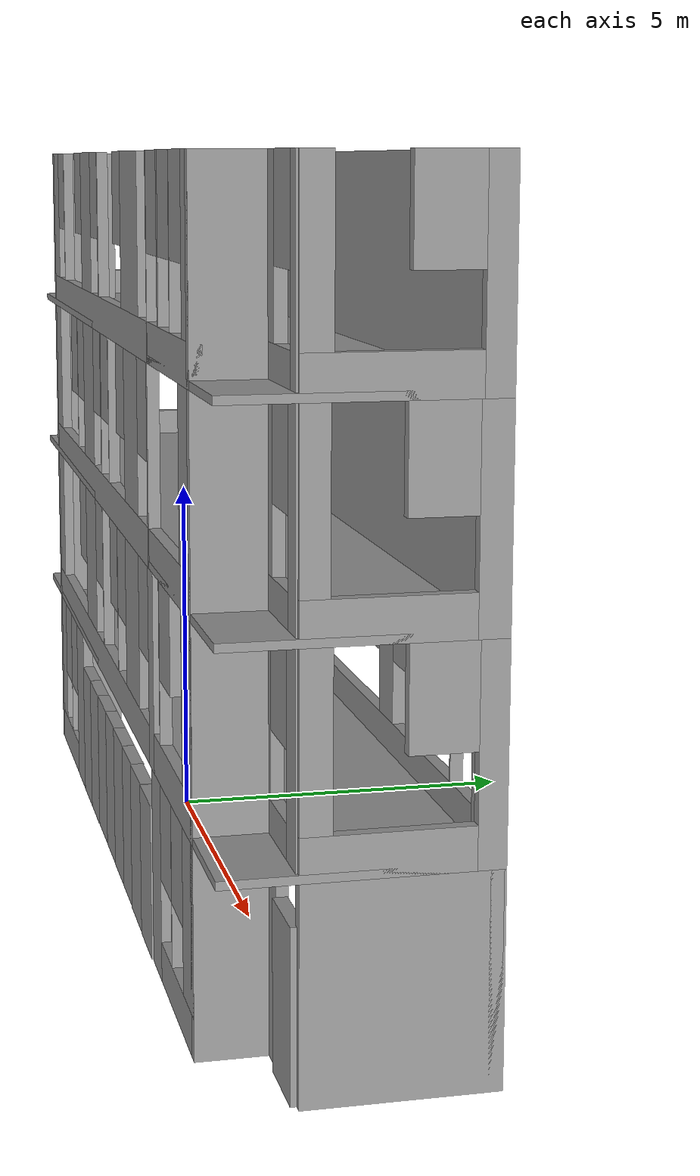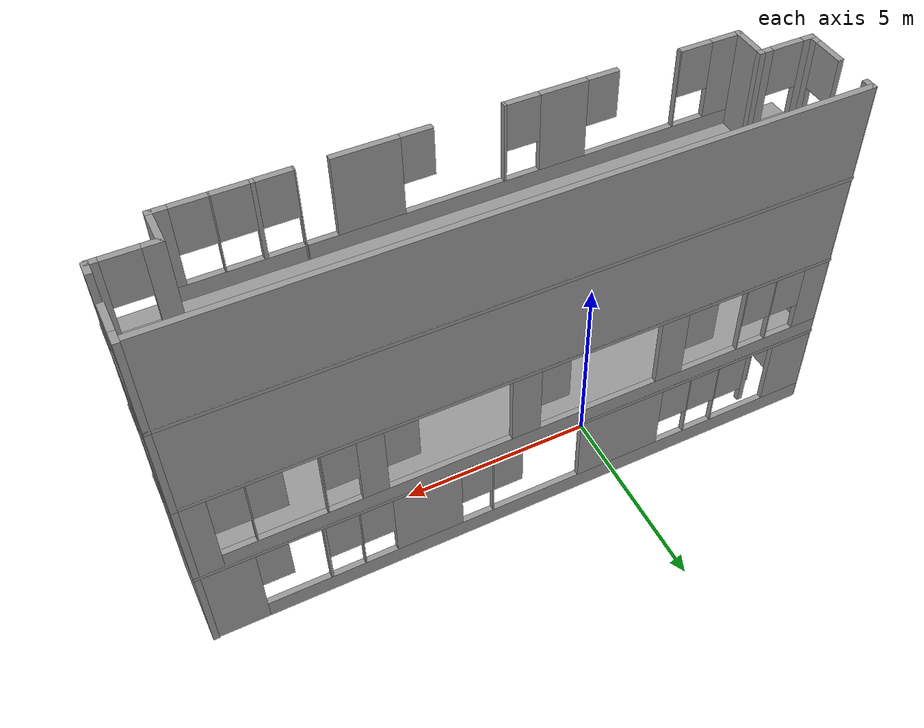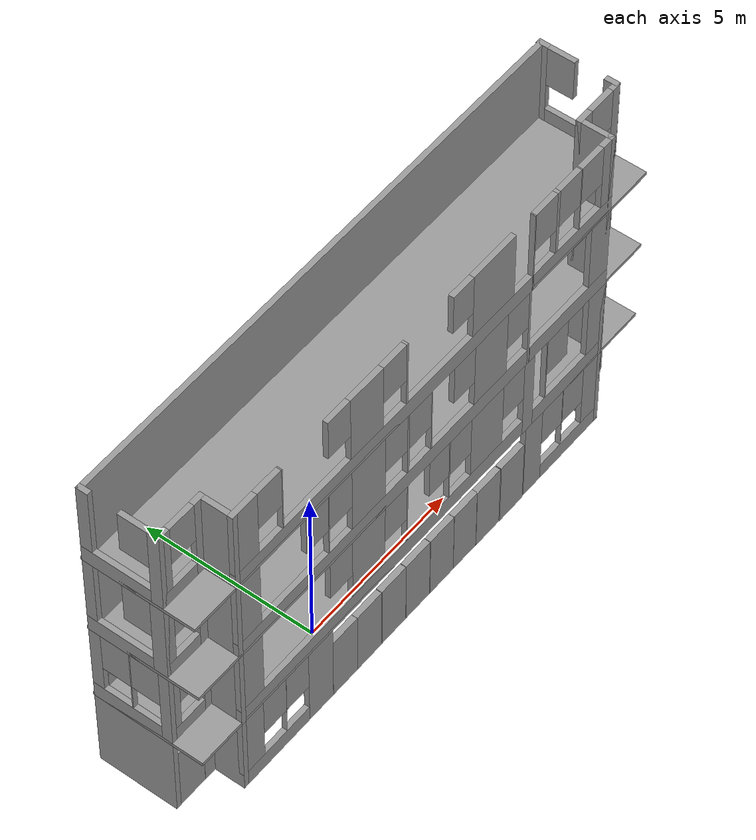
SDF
<?xml version='1.0'?>
<sdf version='1.7'>
  <model name='multimedia'>
    <pose>2.48328 0.104264 0 0 -0 0</pose>
    <link name='Door_0'>
      <collision name='Door_0_Collision'>
        <geometry>
          <box>
            <size>0.9 0.17 2</size>
          </box>
        </geometry>
        <pose>0 0 1 0 -0 0</pose>
      </collision>
      <visual name='Door_0_Visual'>
        <pose>0 0 1 0 -0 0</pose>
        <geometry>
          <box>
            <size>0.9 0.17 2</size>
          </box>
        </geometry>
        <material>
          <script>
            <uri>file://media/materials/scripts/gazebo.material</uri>
            <name>Gazebo/Grey</name>
          </script>
        </material>
      </visual>
      <pose>-1.282 -1.47629 0 0 -0 0</pose>
    </link>
    <link name='Door_1'>
      <collision name='Door_1_Collision'>
        <geometry>
          <box>
            <size>0.9 0.17 2</size>
          </box>
        </geometry>
        <pose>0 0 1 0 -0 0</pose>
      </collision>
      <visual name='Door_1_Visual'>
        <pose>0 0 1 0 -0 0</pose>
        <geometry>
          <box>
            <size>0.9 0.17 2</size>
          </box>
        </geometry>
        <material>
          <script>
            <uri>file://media/materials/scripts/gazebo.material</uri>
            <name>Gazebo/Grey</name>
          </script>
        </material>
      </visual>
      <pose>-0.371814 -1.47629 0 0 -0 0</pose>
    </link>
    <link name='Door_10'>
      <collision name='Door_10_Collision'>
        <geometry>
          <box>
            <size>0.9 0.17 2</size>
          </box>
        </geometry>
        <pose>0 0 1 0 -0 0</pose>
      </collision>
      <visual name='Door_10_Visual'>
        <pose>0 0 1 0 -0 0</pose>
        <geometry>
          <box>
            <size>0.9 0.17 2</size>
          </box>
        </geometry>
        <material>
          <script>
            <uri>file://media/materials/scripts/gazebo.material</uri>
            <name>Gazebo/Grey</name>
          </script>
        </material>
      </visual>
      <pose>3.23662 -1.49446 0 0 -0 0</pose>
    </link>
    <link name='Door_2'>
      <collision name='Door_2_Collision'>
        <geometry>
          <box>
            <size>0.9 0.17 2</size>
          </box>
        </geometry>
        <pose>0 0 1 0 -0 0</pose>
      </collision>
      <visual name='Door_2_Visual'>
        <pose>0 0 1 0 -0 0</pose>
        <geometry>
          <box>
            <size>0.9 0.17 2</size>
          </box>
        </geometry>
        <material>
          <script>
            <uri>file://media/materials/scripts/gazebo.material</uri>
            <name>Gazebo/Grey</name>
          </script>
        </material>
      </visual>
      <pose>-2.19409 -1.48027 0 0 -0 0</pose>
    </link>
    <link name='Door_3'>
      <collision name='Door_3_Collision'>
        <geometry>
          <box>
            <size>0.9 0.17 2</size>
          </box>
        </geometry>
        <pose>0 0 1 0 -0 0</pose>
      </collision>
      <visual name='Door_3_Visual'>
        <pose>0 0 1 0 -0 0</pose>
        <geometry>
          <box>
            <size>0.9 0.17 2</size>
          </box>
        </geometry>
        <material>
          <script>
            <uri>file://media/materials/scripts/gazebo.material</uri>
            <name>Gazebo/Grey</name>
          </script>
        </material>
      </visual>
      <pose>0.536341 -1.48027 0 0 -0 0</pose>
    </link>
    <link name='Door_4'>
      <collision name='Door_4_Collision'>
        <geometry>
          <box>
            <size>0.9 0.17 2</size>
          </box>
        </geometry>
        <pose>0 0 1 0 -0 0</pose>
      </collision>
      <visual name='Door_4_Visual'>
        <pose>0 0 1 0 -0 0</pose>
        <geometry>
          <box>
            <size>0.9 0.17 2</size>
          </box>
        </geometry>
        <material>
          <script>
            <uri>file://media/materials/scripts/gazebo.material</uri>
            <name>Gazebo/Grey</name>
          </script>
        </material>
      </visual>
      <pose>-3.09844 -1.48027 0 0 -0 0</pose>
    </link>
    <link name='Door_5'>
      <collision name='Door_5_Collision'>
        <geometry>
          <box>
            <size>0.9 0.17 2</size>
          </box>
        </geometry>
        <pose>0 0 1 0 -0 0</pose>
      </collision>
      <visual name='Door_5_Visual'>
        <pose>0 0 1 0 -0 0</pose>
        <geometry>
          <box>
            <size>0.9 0.17 2</size>
          </box>
        </geometry>
        <material>
          <script>
            <uri>file://media/materials/scripts/gazebo.material</uri>
            <name>Gazebo/Grey</name>
          </script>
        </material>
      </visual>
      <pose>1.44069 -1.48027 0 0 -0 0</pose>
    </link>
    <link name='Door_7'>
      <collision name='Door_7_Collision'>
        <geometry>
          <box>
            <size>0.9 0.17 2</size>
          </box>
        </geometry>
        <pose>0 0 1 0 -0 0</pose>
      </collision>
      <visual name='Door_7_Visual'>
        <pose>0 0 1 0 -0 0</pose>
        <geometry>
          <box>
            <size>0.9 0.17 2</size>
          </box>
        </geometry>
        <material>
          <script>
            <uri>file://media/materials/scripts/gazebo.material</uri>
            <name>Gazebo/Grey</name>
          </script>
        </material>
      </visual>
      <pose>2.3143 -1.4882 0 0 -0 0</pose>
    </link>
    <link name='Door_8'>
      <collision name='Door_8_Collision'>
        <geometry>
          <box>
            <size>0.9 0.17 2</size>
          </box>
        </geometry>
        <pose>0 0 1 0 -0 0</pose>
      </collision>
      <visual name='Door_8_Visual'>
        <pose>0 0 1 0 -0 0</pose>
        <geometry>
          <box>
            <size>0.9 0.17 2</size>
          </box>
        </geometry>
        <material>
          <script>
            <uri>file://media/materials/scripts/gazebo.material</uri>
            <name>Gazebo/Grey</name>
          </script>
        </material>
      </visual>
      <pose>-7.53633 -0.624894 0 0 -0 0</pose>
    </link>
    <link name='Door_9'>
      <collision name='Door_9_Collision'>
        <geometry>
          <box>
            <size>0.9 0.17 2</size>
          </box>
        </geometry>
        <pose>0 0 1 0 -0 0</pose>
      </collision>
      <visual name='Door_9_Visual'>
        <pose>0 0 1 0 -0 0</pose>
        <geometry>
          <box>
            <size>0.9 0.17 2</size>
          </box>
        </geometry>
        <material>
          <script>
            <uri>file://media/materials/scripts/gazebo.material</uri>
            <name>Gazebo/Grey</name>
          </script>
        </material>
      </visual>
      <pose>7.58444 -0.673203 0 0 -0 0</pose>
    </link>
    <link name='Floor_10'>
      <collision name='Floor_10_Collision'>
        <geometry>
          <box>
            <size>16.2759 3.1264 0.1</size>
          </box>
        </geometry>
        <pose>0 0 0.05 0 -0 0</pose>
      </collision>
      <visual name='Floor_10_Visual'>
        <pose>0 0 0.05 0 -0 0</pose>
        <geometry>
          <box>
            <size>16.2759 3.1264 0.1</size>
          </box>
        </geometry>
        <material>
          <script>
            <uri>file://media/materials/scripts/gazebo.material</uri>
            <name>Gazebo/Grey</name>
          </script>
          <ambient>1 1 1 1</ambient>
        </material>
        <meta>
          <layer>1</layer>
        </meta>
      </visual>
      <pose>0 -0 2.5 0 -0 0</pose>
    </link>
    <link name='Floor_11'>
      <collision name='Floor_11_Collision'>
        <geometry>
          <box>
            <size>16.2759 3.1264 0.1</size>
          </box>
        </geometry>
        <pose>0 0 0.05 0 -0 0</pose>
      </collision>
      <visual name='Floor_11_Visual'>
        <pose>0 0 0.05 0 -0 0</pose>
        <geometry>
          <box>
            <size>16.2759 3.1264 0.1</size>
          </box>
        </geometry>
        <material>
          <script>
            <uri>file://media/materials/scripts/gazebo.material</uri>
            <name>Gazebo/Grey</name>
          </script>
          <ambient>1 1 1 1</ambient>
        </material>
        <meta>
          <layer>2</layer>
        </meta>
      </visual>
      <pose>0 -0 5 0 -0 0</pose>
    </link>
    <link name='Floor_12'>
      <collision name='Floor_12_Collision'>
        <geometry>
          <box>
            <size>16.2759 3.1264 0.1</size>
          </box>
        </geometry>
        <pose>0 0 0.05 0 -0 0</pose>
      </collision>
      <visual name='Floor_12_Visual'>
        <pose>0 0 0.05 0 -0 0</pose>
        <geometry>
          <box>
            <size>16.2759 3.1264 0.1</size>
          </box>
        </geometry>
        <material>
          <script>
            <uri>file://media/materials/scripts/gazebo.material</uri>
            <name>Gazebo/Grey</name>
          </script>
          <ambient>1 1 1 1</ambient>
        </material>
        <meta>
          <layer>3</layer>
        </meta>
      </visual>
      <pose>0 -0 7.5 0 -0 0</pose>
    </link>
    <link name='Wall_100'>
      <collision name='Wall_100_Collision'>
        <geometry>
          <box>
            <size>16.25 0.15 2.5</size>
          </box>
        </geometry>
        <pose>0 0 1.25 0 -0 0</pose>
      </collision>
      <visual name='Wall_100_Visual'>
        <pose>0 0 1.25 0 -0 0</pose>
        <geometry>
          <box>
            <size>16.25 0.15 2.5</size>
          </box>
        </geometry>
        <material>
          <script>
            <uri>file://media/materials/scripts/gazebo.material</uri>
            <name>Gazebo/Grey</name>
          </script>
          <ambient>1 1 1 1</ambient>
        </material>
        <meta>
          <layer>3</layer>
        </meta>
      </visual>
      <pose>0.012948 1.46405 7.5 0 -0 3.14159</pose>
    </link>
    <link name='Wall_101'>
      <pose>-1.5307 -1.4882 7.5 0 -0 3.14159</pose>
      <visual name='Wall_101_Visual_0'>
        <pose>0 0 0.25 0 -0 0</pose>
        <geometry>
          <box>
            <size>10.5 0.15 0.5</size>
          </box>
        </geometry>
        <material>
          <script>
            <uri>file://media/materials/scripts/gazebo.material</uri>
            <name>Gazebo/Grey</name>
          </script>
          <ambient>1 1 1 1</ambient>
        </material>
        <meta>
          <layer>3</layer>
        </meta>
      </visual>
      <collision name='Wall_101_Collision_0'>
        <geometry>
          <box>
            <size>10.5 0.15 0.5</size>
          </box>
        </geometry>
        <pose>0 0 0.25 0 -0 0</pose>
      </collision>
      <visual name='Wall_101_Visual_1'>
        <pose>-3.80135 0 1.5 0 -0 0</pose>
        <geometry>
          <box>
            <size>1.53194 0.15 2</size>
          </box>
        </geometry>
        <material>
          <script>
            <uri>file://media/materials/scripts/gazebo.material</uri>
            <name>Gazebo/Grey</name>
          </script>
          <ambient>1 1 1 1</ambient>
        </material>
        <meta>
          <layer>3</layer>
        </meta>
      </visual>
      <collision name='Wall_101_Collision_1'>
        <geometry>
          <box>
            <size>1.53194 0.15 2</size>
          </box>
        </geometry>
        <pose>-3.80135 0 1.5 0 -0 0</pose>
      </collision>
      <visual name='Wall_101_Visual_2'>
        <pose>-0.670791 0 1.5 0 -0 0</pose>
        <geometry>
          <box>
            <size>0.0625 0.15 2</size>
          </box>
        </geometry>
        <material>
          <script>
            <uri>file://media/materials/scripts/gazebo.material</uri>
            <name>Gazebo/Grey</name>
          </script>
          <ambient>1 1 1 1</ambient>
        </material>
        <meta>
          <layer>3</layer>
        </meta>
      </visual>
      <collision name='Wall_101_Collision_2'>
        <geometry>
          <box>
            <size>0.0625 0.15 2</size>
          </box>
        </geometry>
        <pose>-0.670791 0 1.5 0 -0 0</pose>
      </collision>
      <visual name='Wall_101_Visual_3'>
        <pose>0.734764 0 1.5 0 -0 0</pose>
        <geometry>
          <box>
            <size>1.14861 0.15 2</size>
          </box>
        </geometry>
        <material>
          <script>
            <uri>file://media/materials/scripts/gazebo.material</uri>
            <name>Gazebo/Grey</name>
          </script>
          <ambient>1 1 1 1</ambient>
        </material>
        <meta>
          <layer>3</layer>
        </meta>
      </visual>
      <collision name='Wall_101_Collision_3'>
        <geometry>
          <box>
            <size>1.14861 0.15 2</size>
          </box>
        </geometry>
        <pose>0.734764 0 1.5 0 -0 0</pose>
      </collision>
      <visual name='Wall_101_Visual_4'>
        <pose>3.62574 0 1.5 0 -0 0</pose>
        <geometry>
          <box>
            <size>0.030556 0.15 2</size>
          </box>
        </geometry>
        <material>
          <script>
            <uri>file://media/materials/scripts/gazebo.material</uri>
            <name>Gazebo/Grey</name>
          </script>
          <ambient>1 1 1 1</ambient>
        </material>
        <meta>
          <layer>3</layer>
        </meta>
      </visual>
      <collision name='Wall_101_Collision_4'>
        <geometry>
          <box>
            <size>0.030556 0.15 2</size>
          </box>
        </geometry>
        <pose>3.62574 0 1.5 0 -0 0</pose>
      </collision>
      <visual name='Wall_101_Visual_5'>
        <pose>4.84551 0 1.5 0 -0 0</pose>
        <geometry>
          <box>
            <size>0.808986 0.15 2</size>
          </box>
        </geometry>
        <material>
          <script>
            <uri>file://media/materials/scripts/gazebo.material</uri>
            <name>Gazebo/Grey</name>
          </script>
          <ambient>1 1 1 1</ambient>
        </material>
        <meta>
          <layer>3</layer>
        </meta>
      </visual>
      <collision name='Wall_101_Collision_5'>
        <geometry>
          <box>
            <size>0.808986 0.15 2</size>
          </box>
        </geometry>
        <pose>4.84551 0 1.5 0 -0 0</pose>
      </collision>
      <visual name='Wall_101_Visual_6'>
        <pose>-2.66801 0 1.9 0 -0 0</pose>
        <geometry>
          <box>
            <size>0.734722 0.15 1.2</size>
          </box>
        </geometry>
        <material>
          <script>
            <uri>file://media/materials/scripts/gazebo.material</uri>
            <name>Gazebo/Grey</name>
          </script>
          <ambient>1 1 1 1</ambient>
        </material>
        <meta>
          <layer>3</layer>
        </meta>
      </visual>
      <collision name='Wall_101_Collision_6'>
        <geometry>
          <box>
            <size>0.734722 0.15 1.2</size>
          </box>
        </geometry>
        <pose>-2.66801 0 1.9 0 -0 0</pose>
      </collision>
      <visual name='Wall_101_Visual_7'>
        <pose>-0.239541 0 1.9 0 -0 0</pose>
        <geometry>
          <box>
            <size>0.8 0.15 1.2</size>
          </box>
        </geometry>
        <material>
          <script>
            <uri>file://media/materials/scripts/gazebo.material</uri>
            <name>Gazebo/Grey</name>
          </script>
          <ambient>1 1 1 1</ambient>
        </material>
        <meta>
          <layer>3</layer>
        </meta>
      </visual>
      <collision name='Wall_101_Collision_7'>
        <geometry>
          <box>
            <size>0.8 0.15 1.2</size>
          </box>
        </geometry>
        <pose>-0.239541 0 1.9 0 -0 0</pose>
      </collision>
      <visual name='Wall_101_Visual_8'>
        <pose>1.6924 0 1.9 0 -0 0</pose>
        <geometry>
          <box>
            <size>0.766667 0.15 1.2</size>
          </box>
        </geometry>
        <material>
          <script>
            <uri>file://media/materials/scripts/gazebo.material</uri>
            <name>Gazebo/Grey</name>
          </script>
          <ambient>1 1 1 1</ambient>
        </material>
        <meta>
          <layer>3</layer>
        </meta>
      </visual>
      <collision name='Wall_101_Collision_8'>
        <geometry>
          <box>
            <size>0.766667 0.15 1.2</size>
          </box>
        </geometry>
        <pose>1.6924 0 1.9 0 -0 0</pose>
      </collision>
      <visual name='Wall_101_Visual_9'>
        <pose>4.04101 0 1.9 0 -0 0</pose>
        <geometry>
          <box>
            <size>0.8 0.15 1.2</size>
          </box>
        </geometry>
        <material>
          <script>
            <uri>file://media/materials/scripts/gazebo.material</uri>
            <name>Gazebo/Grey</name>
          </script>
          <ambient>1 1 1 1</ambient>
        </material>
        <meta>
          <layer>3</layer>
        </meta>
      </visual>
      <collision name='Wall_101_Collision_9'>
        <geometry>
          <box>
            <size>0.8 0.15 1.2</size>
          </box>
        </geometry>
        <pose>4.04101 0 1.9 0 -0 0</pose>
      </collision>
    </link>
    <link name='Wall_102'>
      <pose>5.2393 -1.4882 7.5 0 -0 0</pose>
      <visual name='Wall_102_Visual_0'>
        <pose>-1.48398 0 1.25 0 -0 0</pose>
        <geometry>
          <box>
            <size>0.032041 0.15 2.5</size>
          </box>
        </geometry>
        <material>
          <script>
            <uri>file://media/materials/scripts/gazebo.material</uri>
            <name>Gazebo/Grey</name>
          </script>
          <ambient>1 1 1 1</ambient>
        </material>
        <meta>
          <layer>3</layer>
        </meta>
      </visual>
      <collision name='Wall_102_Collision_0'>
        <geometry>
          <box>
            <size>0.032041 0.15 2.5</size>
          </box>
        </geometry>
        <pose>-1.48398 0 1.25 0 -0 0</pose>
      </collision>
      <visual name='Wall_102_Visual_1'>
        <pose>0.016021 0 0.25 0 -0 0</pose>
        <geometry>
          <box>
            <size>2.96796 0.15 0.5</size>
          </box>
        </geometry>
        <material>
          <script>
            <uri>file://media/materials/scripts/gazebo.material</uri>
            <name>Gazebo/Grey</name>
          </script>
          <ambient>1 1 1 1</ambient>
        </material>
        <meta>
          <layer>3</layer>
        </meta>
      </visual>
      <collision name='Wall_102_Collision_1'>
        <geometry>
          <box>
            <size>2.96796 0.15 0.5</size>
          </box>
        </geometry>
        <pose>0.016021 0 0.25 0 -0 0</pose>
      </collision>
      <visual name='Wall_102_Visual_2'>
        <pose>-0.620737 0 1.5 0 -0 0</pose>
        <geometry>
          <box>
            <size>0.094444 0.15 2</size>
          </box>
        </geometry>
        <material>
          <script>
            <uri>file://media/materials/scripts/gazebo.material</uri>
            <name>Gazebo/Grey</name>
          </script>
          <ambient>1 1 1 1</ambient>
        </material>
        <meta>
          <layer>3</layer>
        </meta>
      </visual>
      <collision name='Wall_102_Collision_2'>
        <geometry>
          <box>
            <size>0.094444 0.15 2</size>
          </box>
        </geometry>
        <pose>-0.620737 0 1.5 0 -0 0</pose>
      </collision>
      <visual name='Wall_102_Visual_3'>
        <pose>0.241763 0 1.5 0 -0 0</pose>
        <geometry>
          <box>
            <size>0.030555 0.15 2</size>
          </box>
        </geometry>
        <material>
          <script>
            <uri>file://media/materials/scripts/gazebo.material</uri>
            <name>Gazebo/Grey</name>
          </script>
          <ambient>1 1 1 1</ambient>
        </material>
        <meta>
          <layer>3</layer>
        </meta>
      </visual>
      <collision name='Wall_102_Collision_3'>
        <geometry>
          <box>
            <size>0.030555 0.15 2</size>
          </box>
        </geometry>
        <pose>0.241763 0 1.5 0 -0 0</pose>
      </collision>
      <visual name='Wall_102_Visual_4'>
        <pose>1.27852 0 1.5 0 -0 0</pose>
        <geometry>
          <box>
            <size>0.442959 0.15 2</size>
          </box>
        </geometry>
        <material>
          <script>
            <uri>file://media/materials/scripts/gazebo.material</uri>
            <name>Gazebo/Grey</name>
          </script>
          <ambient>1 1 1 1</ambient>
        </material>
        <meta>
          <layer>3</layer>
        </meta>
      </visual>
      <collision name='Wall_102_Collision_4'>
        <geometry>
          <box>
            <size>0.442959 0.15 2</size>
          </box>
        </geometry>
        <pose>1.27852 0 1.5 0 -0 0</pose>
      </collision>
      <visual name='Wall_102_Visual_5'>
        <pose>-1.06796 0 1.9 0 -0 0</pose>
        <geometry>
          <box>
            <size>0.8 0.15 1.2</size>
          </box>
        </geometry>
        <material>
          <script>
            <uri>file://media/materials/scripts/gazebo.material</uri>
            <name>Gazebo/Grey</name>
          </script>
          <ambient>1 1 1 1</ambient>
        </material>
        <meta>
          <layer>3</layer>
        </meta>
      </visual>
      <collision name='Wall_102_Collision_5'>
        <geometry>
          <box>
            <size>0.8 0.15 1.2</size>
          </box>
        </geometry>
        <pose>-1.06796 0 1.9 0 -0 0</pose>
      </collision>
      <visual name='Wall_102_Visual_6'>
        <pose>-0.173514 0 1.9 0 -0 0</pose>
        <geometry>
          <box>
            <size>0.8 0.15 1.2</size>
          </box>
        </geometry>
        <material>
          <script>
            <uri>file://media/materials/scripts/gazebo.material</uri>
            <name>Gazebo/Grey</name>
          </script>
          <ambient>1 1 1 1</ambient>
        </material>
        <meta>
          <layer>3</layer>
        </meta>
      </visual>
      <collision name='Wall_102_Collision_6'>
        <geometry>
          <box>
            <size>0.8 0.15 1.2</size>
          </box>
        </geometry>
        <pose>-0.173514 0 1.9 0 -0 0</pose>
      </collision>
      <visual name='Wall_102_Visual_7'>
        <pose>0.657041 0 1.9 0 -0 0</pose>
        <geometry>
          <box>
            <size>0.8 0.15 1.2</size>
          </box>
        </geometry>
        <material>
          <script>
            <uri>file://media/materials/scripts/gazebo.material</uri>
            <name>Gazebo/Grey</name>
          </script>
          <ambient>1 1 1 1</ambient>
        </material>
        <meta>
          <layer>3</layer>
        </meta>
      </visual>
      <collision name='Wall_102_Collision_7'>
        <geometry>
          <box>
            <size>0.8 0.15 1.2</size>
          </box>
        </geometry>
        <pose>0.657041 0 1.9 0 -0 0</pose>
      </collision>
    </link>
    <link name='Wall_103'>
      <collision name='Wall_103_Collision'>
        <geometry>
          <box>
            <size>1 0.15 2.5</size>
          </box>
        </geometry>
        <pose>0 0 1.25 0 -0 0</pose>
      </collision>
      <visual name='Wall_103_Visual'>
        <pose>0 0 1.25 0 -0 0</pose>
        <geometry>
          <box>
            <size>1 0.15 2.5</size>
          </box>
        </geometry>
        <material>
          <script>
            <uri>file://media/materials/scripts/gazebo.material</uri>
            <name>Gazebo/Grey</name>
          </script>
          <ambient>1 1 1 1</ambient>
        </material>
        <meta>
          <layer>3</layer>
        </meta>
      </visual>
      <pose>-6.7057 -1.0632 7.5 0 -0 1.5708</pose>
    </link>
    <link name='Wall_104'>
      <pose>-8.06295 0.4118 7.5 0 -0 1.5708</pose>
      <visual name='Wall_104_Visual_0'>
        <pose>-0.963345 0 1.25 0 -0 0</pose>
        <geometry>
          <box>
            <size>0.323309 0.15 2.5</size>
          </box>
        </geometry>
        <material>
          <script>
            <uri>file://media/materials/scripts/gazebo.material</uri>
            <name>Gazebo/Grey</name>
          </script>
          <ambient>1 1 1 1</ambient>
        </material>
        <meta>
          <layer>3</layer>
        </meta>
      </visual>
      <collision name='Wall_104_Collision_0'>
        <geometry>
          <box>
            <size>0.323309 0.15 2.5</size>
          </box>
        </geometry>
        <pose>-0.963345 0 1.25 0 -0 0</pose>
      </collision>
      <visual name='Wall_104_Visual_1'>
        <pose>0.161655 0 0.25 0 -0 0</pose>
        <geometry>
          <box>
            <size>1.92669 0.15 0.5</size>
          </box>
        </geometry>
        <material>
          <script>
            <uri>file://media/materials/scripts/gazebo.material</uri>
            <name>Gazebo/Grey</name>
          </script>
          <ambient>1 1 1 1</ambient>
        </material>
        <meta>
          <layer>3</layer>
        </meta>
      </visual>
      <collision name='Wall_104_Collision_1'>
        <geometry>
          <box>
            <size>1.92669 0.15 0.5</size>
          </box>
        </geometry>
        <pose>0.161655 0 0.25 0 -0 0</pose>
      </collision>
      <visual name='Wall_104_Visual_2'>
        <pose>0.96096 0 1.5 0 -0 0</pose>
        <geometry>
          <box>
            <size>0.32808 0.15 2</size>
          </box>
        </geometry>
        <material>
          <script>
            <uri>file://media/materials/scripts/gazebo.material</uri>
            <name>Gazebo/Grey</name>
          </script>
          <ambient>1 1 1 1</ambient>
        </material>
        <meta>
          <layer>3</layer>
        </meta>
      </visual>
      <collision name='Wall_104_Collision_2'>
        <geometry>
          <box>
            <size>0.32808 0.15 2</size>
          </box>
        </geometry>
        <pose>0.96096 0 1.5 0 -0 0</pose>
      </collision>
      <visual name='Wall_104_Visual_3'>
        <pose>-0.402385 0 1.9 0 -0 0</pose>
        <geometry>
          <box>
            <size>0.798611 0.15 1.2</size>
          </box>
        </geometry>
        <material>
          <script>
            <uri>file://media/materials/scripts/gazebo.material</uri>
            <name>Gazebo/Grey</name>
          </script>
          <ambient>1 1 1 1</ambient>
        </material>
        <meta>
          <layer>3</layer>
        </meta>
      </visual>
      <collision name='Wall_104_Collision_3'>
        <geometry>
          <box>
            <size>0.798611 0.15 1.2</size>
          </box>
        </geometry>
        <pose>-0.402385 0 1.9 0 -0 0</pose>
      </collision>
    </link>
    <link name='Wall_105'>
      <pose>8.06295 0.4382 7.5 0 -0 -1.5708</pose>
      <visual name='Wall_105_Visual_0'>
        <pose>-0.963732 0 1.25 0 -0 0</pose>
        <geometry>
          <box>
            <size>0.322536 0.15 2.5</size>
          </box>
        </geometry>
        <material>
          <script>
            <uri>file://media/materials/scripts/gazebo.material</uri>
            <name>Gazebo/Grey</name>
          </script>
          <ambient>1 1 1 1</ambient>
        </material>
        <meta>
          <layer>3</layer>
        </meta>
      </visual>
      <collision name='Wall_105_Collision_0'>
        <geometry>
          <box>
            <size>0.322536 0.15 2.5</size>
          </box>
        </geometry>
        <pose>-0.963732 0 1.25 0 -0 0</pose>
      </collision>
      <visual name='Wall_105_Visual_1'>
        <pose>0.161268 0 0.25 0 -0 0</pose>
        <geometry>
          <box>
            <size>1.92746 0.15 0.5</size>
          </box>
        </geometry>
        <material>
          <script>
            <uri>file://media/materials/scripts/gazebo.material</uri>
            <name>Gazebo/Grey</name>
          </script>
          <ambient>1 1 1 1</ambient>
        </material>
        <meta>
          <layer>3</layer>
        </meta>
      </visual>
      <collision name='Wall_105_Collision_1'>
        <geometry>
          <box>
            <size>1.92746 0.15 0.5</size>
          </box>
        </geometry>
        <pose>0.161268 0 0.25 0 -0 0</pose>
      </collision>
      <visual name='Wall_105_Visual_2'>
        <pose>0.944601 0 1.5 0 -0 0</pose>
        <geometry>
          <box>
            <size>0.360798 0.15 2</size>
          </box>
        </geometry>
        <material>
          <script>
            <uri>file://media/materials/scripts/gazebo.material</uri>
            <name>Gazebo/Grey</name>
          </script>
          <ambient>1 1 1 1</ambient>
        </material>
        <meta>
          <layer>3</layer>
        </meta>
      </visual>
      <collision name='Wall_105_Collision_2'>
        <geometry>
          <box>
            <size>0.360798 0.15 2</size>
          </box>
        </geometry>
        <pose>0.944601 0 1.5 0 -0 0</pose>
      </collision>
      <visual name='Wall_105_Visual_3'>
        <pose>-0.419131 0 1.9 0 -0 0</pose>
        <geometry>
          <box>
            <size>0.766667 0.15 1.2</size>
          </box>
        </geometry>
        <material>
          <script>
            <uri>file://media/materials/scripts/gazebo.material</uri>
            <name>Gazebo/Grey</name>
          </script>
          <ambient>1 1 1 1</ambient>
        </material>
        <meta>
          <layer>3</layer>
        </meta>
      </visual>
      <collision name='Wall_105_Collision_3'>
        <geometry>
          <box>
            <size>0.766667 0.15 1.2</size>
          </box>
        </geometry>
        <pose>-0.419131 0 1.9 0 -0 0</pose>
      </collision>
    </link>
    <link name='Wall_106'>
      <collision name='Wall_106_Collision'>
        <geometry>
          <box>
            <size>1 0.15 2.5</size>
          </box>
        </geometry>
        <pose>0 0 1.25 0 -0 0</pose>
      </collision>
      <visual name='Wall_106_Visual'>
        <pose>0 0 1.25 0 -0 0</pose>
        <geometry>
          <box>
            <size>1 0.15 2.5</size>
          </box>
        </geometry>
        <material>
          <script>
            <uri>file://media/materials/scripts/gazebo.material</uri>
            <name>Gazebo/Grey</name>
          </script>
          <ambient>1 1 1 1</ambient>
        </material>
        <meta>
          <layer>3</layer>
        </meta>
      </visual>
      <pose>6.6643 -1.0632 7.5 0 -0 1.5708</pose>
    </link>
    <link name='Wall_107'>
      <pose>7.3393 -0.6382 7.5 0 -0 3.14159</pose>
      <visual name='Wall_107_Visual_0'>
        <pose>-0.620187 0 1.25 0 -0 0</pose>
        <geometry>
          <box>
            <size>0.259625 0.15 2.5</size>
          </box>
        </geometry>
        <material>
          <script>
            <uri>file://media/materials/scripts/gazebo.material</uri>
            <name>Gazebo/Grey</name>
          </script>
          <ambient>1 1 1 1</ambient>
        </material>
        <meta>
          <layer>3</layer>
        </meta>
      </visual>
      <collision name='Wall_107_Collision_0'>
        <geometry>
          <box>
            <size>0.259625 0.15 2.5</size>
          </box>
        </geometry>
        <pose>-0.620187 0 1.25 0 -0 0</pose>
      </collision>
      <visual name='Wall_107_Visual_1'>
        <pose>0.129813 0 0.25 0 -0 0</pose>
        <geometry>
          <box>
            <size>1.24038 0.15 0.5</size>
          </box>
        </geometry>
        <material>
          <script>
            <uri>file://media/materials/scripts/gazebo.material</uri>
            <name>Gazebo/Grey</name>
          </script>
          <ambient>1 1 1 1</ambient>
        </material>
        <meta>
          <layer>3</layer>
        </meta>
      </visual>
      <collision name='Wall_107_Collision_1'>
        <geometry>
          <box>
            <size>1.24038 0.15 0.5</size>
          </box>
        </geometry>
        <pose>0.129813 0 0.25 0 -0 0</pose>
      </collision>
      <visual name='Wall_107_Visual_2'>
        <pose>0.529813 0 1.5 0 -0 0</pose>
        <geometry>
          <box>
            <size>0.440375 0.15 2</size>
          </box>
        </geometry>
        <material>
          <script>
            <uri>file://media/materials/scripts/gazebo.material</uri>
            <name>Gazebo/Grey</name>
          </script>
          <ambient>1 1 1 1</ambient>
        </material>
        <meta>
          <layer>3</layer>
        </meta>
      </visual>
      <collision name='Wall_107_Collision_2'>
        <geometry>
          <box>
            <size>0.440375 0.15 2</size>
          </box>
        </geometry>
        <pose>0.529813 0 1.5 0 -0 0</pose>
      </collision>
      <visual name='Wall_107_Visual_3'>
        <pose>-0.090375 0 1.9 0 -0 0</pose>
        <geometry>
          <box>
            <size>0.8 0.15 1.2</size>
          </box>
        </geometry>
        <material>
          <script>
            <uri>file://media/materials/scripts/gazebo.material</uri>
            <name>Gazebo/Grey</name>
          </script>
          <ambient>1 1 1 1</ambient>
        </material>
        <meta>
          <layer>3</layer>
        </meta>
      </visual>
      <collision name='Wall_107_Collision_3'>
        <geometry>
          <box>
            <size>0.8 0.15 1.2</size>
          </box>
        </geometry>
        <pose>-0.090375 0 1.9 0 -0 0</pose>
      </collision>
    </link>
    <link name='Wall_108'>
      <pose>-7.3807 -0.6382 7.5 0 -0 3.14159</pose>
      <visual name='Wall_108_Visual_0'>
        <pose>-0.569076 0 1.25 0 -0 0</pose>
        <geometry>
          <box>
            <size>0.361847 0.15 2.5</size>
          </box>
        </geometry>
        <material>
          <script>
            <uri>file://media/materials/scripts/gazebo.material</uri>
            <name>Gazebo/Grey</name>
          </script>
          <ambient>1 1 1 1</ambient>
        </material>
        <meta>
          <layer>3</layer>
        </meta>
      </visual>
      <collision name='Wall_108_Collision_0'>
        <geometry>
          <box>
            <size>0.361847 0.15 2.5</size>
          </box>
        </geometry>
        <pose>-0.569076 0 1.25 0 -0 0</pose>
      </collision>
      <visual name='Wall_108_Visual_1'>
        <pose>0.180924 0 0.25 0 -0 0</pose>
        <geometry>
          <box>
            <size>1.13815 0.15 0.5</size>
          </box>
        </geometry>
        <material>
          <script>
            <uri>file://media/materials/scripts/gazebo.material</uri>
            <name>Gazebo/Grey</name>
          </script>
          <ambient>1 1 1 1</ambient>
        </material>
        <meta>
          <layer>3</layer>
        </meta>
      </visual>
      <collision name='Wall_108_Collision_1'>
        <geometry>
          <box>
            <size>1.13815 0.15 0.5</size>
          </box>
        </geometry>
        <pose>0.180924 0 0.25 0 -0 0</pose>
      </collision>
      <visual name='Wall_108_Visual_2'>
        <pose>0.580924 0 1.5 0 -0 0</pose>
        <geometry>
          <box>
            <size>0.338153 0.15 2</size>
          </box>
        </geometry>
        <material>
          <script>
            <uri>file://media/materials/scripts/gazebo.material</uri>
            <name>Gazebo/Grey</name>
          </script>
          <ambient>1 1 1 1</ambient>
        </material>
        <meta>
          <layer>3</layer>
        </meta>
      </visual>
      <collision name='Wall_108_Collision_2'>
        <geometry>
          <box>
            <size>0.338153 0.15 2</size>
          </box>
        </geometry>
        <pose>0.580924 0 1.5 0 -0 0</pose>
      </collision>
      <visual name='Wall_108_Visual_3'>
        <pose>0.011847 0 1.9 0 -0 0</pose>
        <geometry>
          <box>
            <size>0.8 0.15 1.2</size>
          </box>
        </geometry>
        <material>
          <script>
            <uri>file://media/materials/scripts/gazebo.material</uri>
            <name>Gazebo/Grey</name>
          </script>
          <ambient>1 1 1 1</ambient>
        </material>
        <meta>
          <layer>3</layer>
        </meta>
      </visual>
      <collision name='Wall_108_Collision_3'>
        <geometry>
          <box>
            <size>0.8 0.15 1.2</size>
          </box>
        </geometry>
        <pose>0.011847 0 1.9 0 -0 0</pose>
      </collision>
    </link>
    <link name='Wall_11'>
      <pose>-5.1557 -1.4882 0 0 -0 3.14159</pose>
      <visual name='Wall_11_Visual_0'>
        <pose>-1.1799 0 1.25 0 -0 0</pose>
        <geometry>
          <box>
            <size>0.890196 0.15 2.5</size>
          </box>
        </geometry>
        <material>
          <script>
            <uri>file://media/materials/scripts/gazebo.material</uri>
            <name>Gazebo/Grey</name>
          </script>
          <ambient>1 1 1 1</ambient>
        </material>
        <meta>
          <layer>0</layer>
        </meta>
      </visual>
      <collision name='Wall_11_Collision_0'>
        <geometry>
          <box>
            <size>0.890196 0.15 2.5</size>
          </box>
        </geometry>
        <pose>-1.1799 0 1.25 0 -0 0</pose>
      </collision>
      <visual name='Wall_11_Visual_1'>
        <pose>0.445098 0 0.25 0 -0 0</pose>
        <geometry>
          <box>
            <size>2.3598 0.15 0.5</size>
          </box>
        </geometry>
        <material>
          <script>
            <uri>file://media/materials/scripts/gazebo.material</uri>
            <name>Gazebo/Grey</name>
          </script>
          <ambient>1 1 1 1</ambient>
        </material>
        <meta>
          <layer>0</layer>
        </meta>
      </visual>
      <collision name='Wall_11_Collision_1'>
        <geometry>
          <box>
            <size>2.3598 0.15 0.5</size>
          </box>
        </geometry>
        <pose>0.445098 0 0.25 0 -0 0</pose>
      </collision>
      <visual name='Wall_11_Visual_2'>
        <pose>0.067696 0 1.5 0 -0 0</pose>
        <geometry>
          <box>
            <size>0.005 0.15 2</size>
          </box>
        </geometry>
        <material>
          <script>
            <uri>file://media/materials/scripts/gazebo.material</uri>
            <name>Gazebo/Grey</name>
          </script>
          <ambient>1 1 1 1</ambient>
        </material>
        <meta>
          <layer>0</layer>
        </meta>
      </visual>
      <collision name='Wall_11_Collision_2'>
        <geometry>
          <box>
            <size>0.005 0.15 2</size>
          </box>
        </geometry>
        <pose>0.067696 0 1.5 0 -0 0</pose>
      </collision>
      <visual name='Wall_11_Visual_3'>
        <pose>1.2476 0 1.5 0 -0 0</pose>
        <geometry>
          <box>
            <size>0.754804 0.15 2</size>
          </box>
        </geometry>
        <material>
          <script>
            <uri>file://media/materials/scripts/gazebo.material</uri>
            <name>Gazebo/Grey</name>
          </script>
          <ambient>1 1 1 1</ambient>
        </material>
        <meta>
          <layer>0</layer>
        </meta>
      </visual>
      <collision name='Wall_11_Collision_3'>
        <geometry>
          <box>
            <size>0.754804 0.15 2</size>
          </box>
        </geometry>
        <pose>1.2476 0 1.5 0 -0 0</pose>
      </collision>
      <visual name='Wall_11_Visual_4'>
        <pose>-0.334804 0 1.9 0 -0 0</pose>
        <geometry>
          <box>
            <size>0.8 0.15 1.2</size>
          </box>
        </geometry>
        <material>
          <script>
            <uri>file://media/materials/scripts/gazebo.material</uri>
            <name>Gazebo/Grey</name>
          </script>
          <ambient>1 1 1 1</ambient>
        </material>
        <meta>
          <layer>0</layer>
        </meta>
      </visual>
      <collision name='Wall_11_Collision_4'>
        <geometry>
          <box>
            <size>0.8 0.15 1.2</size>
          </box>
        </geometry>
        <pose>-0.334804 0 1.9 0 -0 0</pose>
      </collision>
      <visual name='Wall_11_Visual_5'>
        <pose>0.470196 0 1.9 0 -0 0</pose>
        <geometry>
          <box>
            <size>0.8 0.15 1.2</size>
          </box>
        </geometry>
        <material>
          <script>
            <uri>file://media/materials/scripts/gazebo.material</uri>
            <name>Gazebo/Grey</name>
          </script>
          <ambient>1 1 1 1</ambient>
        </material>
        <meta>
          <layer>0</layer>
        </meta>
      </visual>
      <collision name='Wall_11_Collision_5'>
        <geometry>
          <box>
            <size>0.8 0.15 1.2</size>
          </box>
        </geometry>
        <pose>0.470196 0 1.9 0 -0 0</pose>
      </collision>
    </link>
    <link name='Wall_13'>
      <pose>5.2393 -1.4882 0 0 -0 0</pose>
      <visual name='Wall_13_Visual_0'>
        <pose>-1.16632 0 1.25 0 -0 0</pose>
        <geometry>
          <box>
            <size>0.667366 0.15 2.5</size>
          </box>
        </geometry>
        <material>
          <script>
            <uri>file://media/materials/scripts/gazebo.material</uri>
            <name>Gazebo/Grey</name>
          </script>
          <ambient>1 1 1 1</ambient>
        </material>
        <meta>
          <layer>0</layer>
        </meta>
      </visual>
      <collision name='Wall_13_Collision_0'>
        <geometry>
          <box>
            <size>0.667366 0.15 2.5</size>
          </box>
        </geometry>
        <pose>-1.16632 0 1.25 0 -0 0</pose>
      </collision>
      <visual name='Wall_13_Visual_1'>
        <pose>0.333683 0 0.25 0 -0 0</pose>
        <geometry>
          <box>
            <size>2.33263 0.15 0.5</size>
          </box>
        </geometry>
        <material>
          <script>
            <uri>file://media/materials/scripts/gazebo.material</uri>
            <name>Gazebo/Grey</name>
          </script>
          <ambient>1 1 1 1</ambient>
        </material>
        <meta>
          <layer>0</layer>
        </meta>
      </visual>
      <collision name='Wall_13_Collision_1'>
        <geometry>
          <box>
            <size>2.33263 0.15 0.5</size>
          </box>
        </geometry>
        <pose>0.333683 0 0.25 0 -0 0</pose>
      </collision>
      <visual name='Wall_13_Visual_2'>
        <pose>-0.022006 0 1.5 0 -0 0</pose>
        <geometry>
          <box>
            <size>0.021256 0.15 2</size>
          </box>
        </geometry>
        <material>
          <script>
            <uri>file://media/materials/scripts/gazebo.material</uri>
            <name>Gazebo/Grey</name>
          </script>
          <ambient>1 1 1 1</ambient>
        </material>
        <meta>
          <layer>0</layer>
        </meta>
      </visual>
      <collision name='Wall_13_Collision_2'>
        <geometry>
          <box>
            <size>0.021256 0.15 2</size>
          </box>
        </geometry>
        <pose>-0.022006 0 1.5 0 -0 0</pose>
      </collision>
      <visual name='Wall_13_Visual_3'>
        <pose>1.14431 0 1.5 0 -0 0</pose>
        <geometry>
          <box>
            <size>0.711378 0.15 2</size>
          </box>
        </geometry>
        <material>
          <script>
            <uri>file://media/materials/scripts/gazebo.material</uri>
            <name>Gazebo/Grey</name>
          </script>
          <ambient>1 1 1 1</ambient>
        </material>
        <meta>
          <layer>0</layer>
        </meta>
      </visual>
      <collision name='Wall_13_Collision_3'>
        <geometry>
          <box>
            <size>0.711378 0.15 2</size>
          </box>
        </geometry>
        <pose>1.14431 0 1.5 0 -0 0</pose>
      </collision>
      <visual name='Wall_13_Visual_4'>
        <pose>-0.432634 0 1.9 0 -0 0</pose>
        <geometry>
          <box>
            <size>0.8 0.15 1.2</size>
          </box>
        </geometry>
        <material>
          <script>
            <uri>file://media/materials/scripts/gazebo.material</uri>
            <name>Gazebo/Grey</name>
          </script>
          <ambient>1 1 1 1</ambient>
        </material>
        <meta>
          <layer>0</layer>
        </meta>
      </visual>
      <collision name='Wall_13_Collision_4'>
        <geometry>
          <box>
            <size>0.8 0.15 1.2</size>
          </box>
        </geometry>
        <pose>-0.432634 0 1.9 0 -0 0</pose>
      </collision>
      <visual name='Wall_13_Visual_5'>
        <pose>0.388622 0 1.9 0 -0 0</pose>
        <geometry>
          <box>
            <size>0.8 0.15 1.2</size>
          </box>
        </geometry>
        <material>
          <script>
            <uri>file://media/materials/scripts/gazebo.material</uri>
            <name>Gazebo/Grey</name>
          </script>
          <ambient>1 1 1 1</ambient>
        </material>
        <meta>
          <layer>0</layer>
        </meta>
      </visual>
      <collision name='Wall_13_Collision_5'>
        <geometry>
          <box>
            <size>0.8 0.15 1.2</size>
          </box>
        </geometry>
        <pose>0.388622 0 1.9 0 -0 0</pose>
      </collision>
    </link>
    <link name='Wall_2'>
      <pose>0.012948 1.46405 0 0 -0 3.14159</pose>
      <visual name='Wall_2_Visual_0'>
        <pose>-7.42781 0 1.25 0 -0 0</pose>
        <geometry>
          <box>
            <size>1.39439 0.15 2.5</size>
          </box>
        </geometry>
        <material>
          <script>
            <uri>file://media/materials/scripts/gazebo.material</uri>
            <name>Gazebo/Grey</name>
          </script>
          <ambient>1 1 1 1</ambient>
        </material>
        <meta>
          <layer>0</layer>
        </meta>
      </visual>
      <collision name='Wall_2_Collision_0'>
        <geometry>
          <box>
            <size>1.39439 0.15 2.5</size>
          </box>
        </geometry>
        <pose>-7.42781 0 1.25 0 -0 0</pose>
      </collision>
      <visual name='Wall_2_Visual_1'>
        <pose>0.697193 0 0.25 0 -0 0</pose>
        <geometry>
          <box>
            <size>14.8556 0.15 0.5</size>
          </box>
        </geometry>
        <material>
          <script>
            <uri>file://media/materials/scripts/gazebo.material</uri>
            <name>Gazebo/Grey</name>
          </script>
          <ambient>1 1 1 1</ambient>
        </material>
        <meta>
          <layer>0</layer>
        </meta>
      </visual>
      <collision name='Wall_2_Collision_1'>
        <geometry>
          <box>
            <size>14.8556 0.15 0.5</size>
          </box>
        </geometry>
        <pose>0.697193 0 0.25 0 -0 0</pose>
      </collision>
      <visual name='Wall_2_Visual_2'>
        <pose>-5.1327 0 1.5 0 -0 0</pose>
        <geometry>
          <box>
            <size>0.0625 0.15 2</size>
          </box>
        </geometry>
        <material>
          <script>
            <uri>file://media/materials/scripts/gazebo.material</uri>
            <name>Gazebo/Grey</name>
          </script>
          <ambient>1 1 1 1</ambient>
        </material>
        <meta>
          <layer>0</layer>
        </meta>
      </visual>
      <collision name='Wall_2_Collision_2'>
        <geometry>
          <box>
            <size>0.0625 0.15 2</size>
          </box>
        </geometry>
        <pose>-5.1327 0 1.5 0 -0 0</pose>
      </collision>
      <visual name='Wall_2_Visual_3'>
        <pose>-4.28617 0 1.5 0 -0 0</pose>
        <geometry>
          <box>
            <size>0.030556 0.15 2</size>
          </box>
        </geometry>
        <material>
          <script>
            <uri>file://media/materials/scripts/gazebo.material</uri>
            <name>Gazebo/Grey</name>
          </script>
          <ambient>1 1 1 1</ambient>
        </material>
        <meta>
          <layer>0</layer>
        </meta>
      </visual>
      <collision name='Wall_2_Collision_3'>
        <geometry>
          <box>
            <size>0.030556 0.15 2</size>
          </box>
        </geometry>
        <pose>-4.28617 0 1.5 0 -0 0</pose>
      </collision>
      <visual name='Wall_2_Visual_4'>
        <pose>-2.60909 0 1.5 0 -0 0</pose>
        <geometry>
          <box>
            <size>1.72361 0.15 2</size>
          </box>
        </geometry>
        <material>
          <script>
            <uri>file://media/materials/scripts/gazebo.material</uri>
            <name>Gazebo/Grey</name>
          </script>
          <ambient>1 1 1 1</ambient>
        </material>
        <meta>
          <layer>0</layer>
        </meta>
      </visual>
      <collision name='Wall_2_Collision_4'>
        <geometry>
          <box>
            <size>1.72361 0.15 2</size>
          </box>
        </geometry>
        <pose>-2.60909 0 1.5 0 -0 0</pose>
      </collision>
      <visual name='Wall_2_Visual_5'>
        <pose>-0.932003 0 1.5 0 -0 0</pose>
        <geometry>
          <box>
            <size>0.030555 0.15 2</size>
          </box>
        </geometry>
        <material>
          <script>
            <uri>file://media/materials/scripts/gazebo.material</uri>
            <name>Gazebo/Grey</name>
          </script>
          <ambient>1 1 1 1</ambient>
        </material>
        <meta>
          <layer>0</layer>
        </meta>
      </visual>
      <collision name='Wall_2_Collision_5'>
        <geometry>
          <box>
            <size>0.030555 0.15 2</size>
          </box>
        </geometry>
        <pose>-0.932003 0 1.5 0 -0 0</pose>
      </collision>
      <visual name='Wall_2_Visual_6'>
        <pose>2.56591 0 1.5 0 -0 0</pose>
        <geometry>
          <box>
            <size>2.29861 0.15 2</size>
          </box>
        </geometry>
        <material>
          <script>
            <uri>file://media/materials/scripts/gazebo.material</uri>
            <name>Gazebo/Grey</name>
          </script>
          <ambient>1 1 1 1</ambient>
        </material>
        <meta>
          <layer>0</layer>
        </meta>
      </visual>
      <collision name='Wall_2_Collision_6'>
        <geometry>
          <box>
            <size>2.29861 0.15 2</size>
          </box>
        </geometry>
        <pose>2.56591 0 1.5 0 -0 0</pose>
      </collision>
      <visual name='Wall_2_Visual_7'>
        <pose>4.5305 0 1.5 0 -0 0</pose>
        <geometry>
          <box>
            <size>0.030556 0.15 2</size>
          </box>
        </geometry>
        <material>
          <script>
            <uri>file://media/materials/scripts/gazebo.material</uri>
            <name>Gazebo/Grey</name>
          </script>
          <ambient>1 1 1 1</ambient>
        </material>
        <meta>
          <layer>0</layer>
        </meta>
      </visual>
      <collision name='Wall_2_Collision_7'>
        <geometry>
          <box>
            <size>0.030556 0.15 2</size>
          </box>
        </geometry>
        <pose>4.5305 0 1.5 0 -0 0</pose>
      </collision>
      <visual name='Wall_2_Visual_8'>
        <pose>5.36105 0 1.5 0 -0 0</pose>
        <geometry>
          <box>
            <size>0.030555 0.15 2</size>
          </box>
        </geometry>
        <material>
          <script>
            <uri>file://media/materials/scripts/gazebo.material</uri>
            <name>Gazebo/Grey</name>
          </script>
          <ambient>1 1 1 1</ambient>
        </material>
        <meta>
          <layer>0</layer>
        </meta>
      </visual>
      <collision name='Wall_2_Collision_8'>
        <geometry>
          <box>
            <size>0.030555 0.15 2</size>
          </box>
        </geometry>
        <pose>5.36105 0 1.5 0 -0 0</pose>
      </collision>
      <visual name='Wall_2_Visual_9'>
        <pose>7.54997 0 1.5 0 -0 0</pose>
        <geometry>
          <box>
            <size>1.15006 0.15 2</size>
          </box>
        </geometry>
        <material>
          <script>
            <uri>file://media/materials/scripts/gazebo.material</uri>
            <name>Gazebo/Grey</name>
          </script>
          <ambient>1 1 1 1</ambient>
        </material>
        <meta>
          <layer>0</layer>
        </meta>
      </visual>
      <collision name='Wall_2_Collision_9'>
        <geometry>
          <box>
            <size>1.15006 0.15 2</size>
          </box>
        </geometry>
        <pose>7.54997 0 1.5 0 -0 0</pose>
      </collision>
      <visual name='Wall_2_Visual_10'>
        <pose>-6.34728 0 1.9 0 -0 0</pose>
        <geometry>
          <box>
            <size>0.766666 0.15 1.2</size>
          </box>
        </geometry>
        <material>
          <script>
            <uri>file://media/materials/scripts/gazebo.material</uri>
            <name>Gazebo/Grey</name>
          </script>
          <ambient>1 1 1 1</ambient>
        </material>
        <meta>
          <layer>0</layer>
        </meta>
      </visual>
      <collision name='Wall_2_Collision_10'>
        <geometry>
          <box>
            <size>0.766666 0.15 1.2</size>
          </box>
        </geometry>
        <pose>-6.34728 0 1.9 0 -0 0</pose>
      </collision>
      <visual name='Wall_2_Visual_11'>
        <pose>-4.70145 0 1.9 0 -0 0</pose>
        <geometry>
          <box>
            <size>0.8 0.15 1.2</size>
          </box>
        </geometry>
        <material>
          <script>
            <uri>file://media/materials/scripts/gazebo.material</uri>
            <name>Gazebo/Grey</name>
          </script>
          <ambient>1 1 1 1</ambient>
        </material>
        <meta>
          <layer>0</layer>
        </meta>
      </visual>
      <collision name='Wall_2_Collision_11'>
        <geometry>
          <box>
            <size>0.8 0.15 1.2</size>
          </box>
        </geometry>
        <pose>-4.70145 0 1.9 0 -0 0</pose>
      </collision>
      <visual name='Wall_2_Visual_12'>
        <pose>-3.87089 0 1.9 0 -0 0</pose>
        <geometry>
          <box>
            <size>0.8 0.15 1.2</size>
          </box>
        </geometry>
        <material>
          <script>
            <uri>file://media/materials/scripts/gazebo.material</uri>
            <name>Gazebo/Grey</name>
          </script>
          <ambient>1 1 1 1</ambient>
        </material>
        <meta>
          <layer>0</layer>
        </meta>
      </visual>
      <collision name='Wall_2_Collision_12'>
        <geometry>
          <box>
            <size>0.8 0.15 1.2</size>
          </box>
        </geometry>
        <pose>-3.87089 0 1.9 0 -0 0</pose>
      </collision>
      <visual name='Wall_2_Visual_13'>
        <pose>-1.34728 0 1.9 0 -0 0</pose>
        <geometry>
          <box>
            <size>0.8 0.15 1.2</size>
          </box>
        </geometry>
        <material>
          <script>
            <uri>file://media/materials/scripts/gazebo.material</uri>
            <name>Gazebo/Grey</name>
          </script>
          <ambient>1 1 1 1</ambient>
        </material>
        <meta>
          <layer>0</layer>
        </meta>
      </visual>
      <collision name='Wall_2_Collision_13'>
        <geometry>
          <box>
            <size>0.8 0.15 1.2</size>
          </box>
        </geometry>
        <pose>-1.34728 0 1.9 0 -0 0</pose>
      </collision>
      <visual name='Wall_2_Visual_14'>
        <pose>-0.533392 0 1.9 0 -0 0</pose>
        <geometry>
          <box>
            <size>0.766667 0.15 1.2</size>
          </box>
        </geometry>
        <material>
          <script>
            <uri>file://media/materials/scripts/gazebo.material</uri>
            <name>Gazebo/Grey</name>
          </script>
          <ambient>1 1 1 1</ambient>
        </material>
        <meta>
          <layer>0</layer>
        </meta>
      </visual>
      <collision name='Wall_2_Collision_14'>
        <geometry>
          <box>
            <size>0.766667 0.15 1.2</size>
          </box>
        </geometry>
        <pose>-0.533392 0 1.9 0 -0 0</pose>
      </collision>
      <visual name='Wall_2_Visual_15'>
        <pose>4.11522 0 1.9 0 -0 0</pose>
        <geometry>
          <box>
            <size>0.8 0.15 1.2</size>
          </box>
        </geometry>
        <material>
          <script>
            <uri>file://media/materials/scripts/gazebo.material</uri>
            <name>Gazebo/Grey</name>
          </script>
          <ambient>1 1 1 1</ambient>
        </material>
        <meta>
          <layer>0</layer>
        </meta>
      </visual>
      <collision name='Wall_2_Collision_15'>
        <geometry>
          <box>
            <size>0.8 0.15 1.2</size>
          </box>
        </geometry>
        <pose>4.11522 0 1.9 0 -0 0</pose>
      </collision>
      <visual name='Wall_2_Visual_16'>
        <pose>4.94578 0 1.9 0 -0 0</pose>
        <geometry>
          <box>
            <size>0.8 0.15 1.2</size>
          </box>
        </geometry>
        <material>
          <script>
            <uri>file://media/materials/scripts/gazebo.material</uri>
            <name>Gazebo/Grey</name>
          </script>
          <ambient>1 1 1 1</ambient>
        </material>
        <meta>
          <layer>0</layer>
        </meta>
      </visual>
      <collision name='Wall_2_Collision_16'>
        <geometry>
          <box>
            <size>0.8 0.15 1.2</size>
          </box>
        </geometry>
        <pose>4.94578 0 1.9 0 -0 0</pose>
      </collision>
      <visual name='Wall_2_Visual_17'>
        <pose>5.77564 0 1.9 0 -0 0</pose>
        <geometry>
          <box>
            <size>0.798611 0.15 1.2</size>
          </box>
        </geometry>
        <material>
          <script>
            <uri>file://media/materials/scripts/gazebo.material</uri>
            <name>Gazebo/Grey</name>
          </script>
          <ambient>1 1 1 1</ambient>
        </material>
        <meta>
          <layer>0</layer>
        </meta>
      </visual>
      <collision name='Wall_2_Collision_17'>
        <geometry>
          <box>
            <size>0.798611 0.15 1.2</size>
          </box>
        </geometry>
        <pose>5.77564 0 1.9 0 -0 0</pose>
      </collision>
    </link>
    <link name='Wall_45'>
      <collision name='Wall_45_Collision'>
        <geometry>
          <box>
            <size>1 0.15 2.5</size>
          </box>
        </geometry>
        <pose>0 0 1.25 0 -0 0</pose>
      </collision>
      <visual name='Wall_45_Visual'>
        <pose>0 0 1.25 0 -0 0</pose>
        <geometry>
          <box>
            <size>1 0.15 2.5</size>
          </box>
        </geometry>
        <material>
          <script>
            <uri>file://media/materials/scripts/gazebo.material</uri>
            <name>Gazebo/Grey</name>
          </script>
          <ambient>1 1 1 1</ambient>
        </material>
        <meta>
          <layer>0</layer>
        </meta>
      </visual>
      <pose>-6.7057 -1.0632 0 0 -0 1.5708</pose>
    </link>
    <link name='Wall_51'>
      <collision name='Wall_51_Collision'>
        <geometry>
          <box>
            <size>0.15 0.15 2.5</size>
          </box>
        </geometry>
        <pose>0 0 1.25 0 -0 0</pose>
      </collision>
      <visual name='Wall_51_Visual'>
        <pose>0 0 1.25 0 -0 0</pose>
        <geometry>
          <box>
            <size>0.15 0.15 2.5</size>
          </box>
        </geometry>
        <material>
          <script>
            <uri>file://media/materials/scripts/gazebo.material</uri>
            <name>Gazebo/Grey</name>
          </script>
          <ambient>0 0 0 1</ambient>
        </material>
        <meta>
          <layer>0</layer>
        </meta>
      </visual>
      <pose>-6.74318 0.927099 0 0 -0 0</pose>
    </link>
    <link name='Wall_54'>
      <collision name='Wall_54_Collision'>
        <geometry>
          <box>
            <size>0.15 0.15 2.5</size>
          </box>
        </geometry>
        <pose>0 0 1.25 0 -0 0</pose>
      </collision>
      <visual name='Wall_54_Visual'>
        <pose>0 0 1.25 0 -0 0</pose>
        <geometry>
          <box>
            <size>0.15 0.15 2.5</size>
          </box>
        </geometry>
        <material>
          <script>
            <uri>file://media/materials/scripts/gazebo.material</uri>
            <name>Gazebo/Grey</name>
          </script>
          <ambient>0 0 0 1</ambient>
        </material>
        <meta>
          <layer>0</layer>
        </meta>
      </visual>
      <pose>-7.23328 0.463108 0 0 -0 0</pose>
    </link>
    <link name='Wall_61'>
      <collision name='Wall_61_Collision'>
        <geometry>
          <box>
            <size>2.25 0.15 2.5</size>
          </box>
        </geometry>
        <pose>0 0 1.25 0 -0 0</pose>
      </collision>
      <visual name='Wall_61_Visual'>
        <pose>0 0 1.25 0 -0 0</pose>
        <geometry>
          <box>
            <size>2.25 0.15 2.5</size>
          </box>
        </geometry>
        <material>
          <script>
            <uri>file://media/materials/scripts/gazebo.material</uri>
            <name>Gazebo/Grey</name>
          </script>
          <ambient>1 1 1 1</ambient>
        </material>
        <meta>
          <layer>0</layer>
        </meta>
      </visual>
      <pose>-8.06295 0.4118 0 0 -0 1.5708</pose>
    </link>
    <link name='Wall_65'>
      <collision name='Wall_65_Collision'>
        <geometry>
          <box>
            <size>2.25 0.15 2.5</size>
          </box>
        </geometry>
        <pose>0 0 1.25 0 -0 0</pose>
      </collision>
      <visual name='Wall_65_Visual'>
        <pose>0 0 1.25 0 -0 0</pose>
        <geometry>
          <box>
            <size>2.25 0.15 2.5</size>
          </box>
        </geometry>
        <material>
          <script>
            <uri>file://media/materials/scripts/gazebo.material</uri>
            <name>Gazebo/Grey</name>
          </script>
          <ambient>1 1 1 1</ambient>
        </material>
        <meta>
          <layer>0</layer>
        </meta>
      </visual>
      <pose>8.06295 0.4382 0 0 -0 -1.5708</pose>
    </link>
    <link name='Wall_67'>
      <collision name='Wall_67_Collision'>
        <geometry>
          <box>
            <size>1 0.15 2.5</size>
          </box>
        </geometry>
        <pose>0 0 1.25 0 -0 0</pose>
      </collision>
      <visual name='Wall_67_Visual'>
        <pose>0 0 1.25 0 -0 0</pose>
        <geometry>
          <box>
            <size>1 0.15 2.5</size>
          </box>
        </geometry>
        <material>
          <script>
            <uri>file://media/materials/scripts/gazebo.material</uri>
            <name>Gazebo/Grey</name>
          </script>
          <ambient>1 1 1 1</ambient>
        </material>
        <meta>
          <layer>0</layer>
        </meta>
      </visual>
      <pose>6.6643 -1.0632 0 0 -0 1.5708</pose>
    </link>
    <link name='Wall_69'>
      <collision name='Wall_69_Collision'>
        <geometry>
          <box>
            <size>0.5 0.15 2.5</size>
          </box>
        </geometry>
        <pose>0 0 1.25 0 -0 0</pose>
      </collision>
      <visual name='Wall_69_Visual'>
        <pose>0 0 1.25 0 -0 0</pose>
        <geometry>
          <box>
            <size>0.5 0.15 2.5</size>
          </box>
        </geometry>
        <material>
          <script>
            <uri>file://media/materials/scripts/gazebo.material</uri>
            <name>Gazebo/Grey</name>
          </script>
          <ambient>1 1 1 1</ambient>
        </material>
        <meta>
          <layer>0</layer>
        </meta>
      </visual>
      <pose>6.8393 -0.6382 0 0 -0 3.14159</pose>
    </link>
    <link name='Wall_71'>
      <collision name='Wall_71_Collision'>
        <geometry>
          <box>
            <size>0.5 0.15 2.5</size>
          </box>
        </geometry>
        <pose>0 0 1.25 0 -0 0</pose>
      </collision>
      <visual name='Wall_71_Visual'>
        <pose>0 0 1.25 0 -0 0</pose>
        <geometry>
          <box>
            <size>0.5 0.15 2.5</size>
          </box>
        </geometry>
        <material>
          <script>
            <uri>file://media/materials/scripts/gazebo.material</uri>
            <name>Gazebo/Grey</name>
          </script>
          <ambient>1 1 1 1</ambient>
        </material>
        <meta>
          <layer>0</layer>
        </meta>
      </visual>
      <pose>-6.8807 -0.6382 0 0 -0 3.14159</pose>
    </link>
    <link name='Wall_82'>
      <pose>0.012948 1.46405 2.5 0 -0 3.14159</pose>
      <visual name='Wall_82_Visual_0'>
        <pose>-7.76322 0 1.25 0 -0 0</pose>
        <geometry>
          <box>
            <size>0.723552 0.15 2.5</size>
          </box>
        </geometry>
        <material>
          <script>
            <uri>file://media/materials/scripts/gazebo.material</uri>
            <name>Gazebo/Grey</name>
          </script>
          <ambient>1 1 1 1</ambient>
        </material>
        <meta>
          <layer>1</layer>
        </meta>
      </visual>
      <collision name='Wall_82_Collision_0'>
        <geometry>
          <box>
            <size>0.723552 0.15 2.5</size>
          </box>
        </geometry>
        <pose>-7.76322 0 1.25 0 -0 0</pose>
      </collision>
      <visual name='Wall_82_Visual_1'>
        <pose>0.361776 0 0.25 0 -0 0</pose>
        <geometry>
          <box>
            <size>15.5264 0.15 0.5</size>
          </box>
        </geometry>
        <material>
          <script>
            <uri>file://media/materials/scripts/gazebo.material</uri>
            <name>Gazebo/Grey</name>
          </script>
          <ambient>1 1 1 1</ambient>
        </material>
        <meta>
          <layer>1</layer>
        </meta>
      </visual>
      <collision name='Wall_82_Collision_1'>
        <geometry>
          <box>
            <size>15.5264 0.15 0.5</size>
          </box>
        </geometry>
        <pose>0.361776 0 0.25 0 -0 0</pose>
      </collision>
      <visual name='Wall_82_Visual_2'>
        <pose>-6.58617 0 1.5 0 -0 0</pose>
        <geometry>
          <box>
            <size>0.030556 0.15 2</size>
          </box>
        </geometry>
        <material>
          <script>
            <uri>file://media/materials/scripts/gazebo.material</uri>
            <name>Gazebo/Grey</name>
          </script>
          <ambient>1 1 1 1</ambient>
        </material>
        <meta>
          <layer>1</layer>
        </meta>
      </visual>
      <collision name='Wall_82_Collision_2'>
        <geometry>
          <box>
            <size>0.030556 0.15 2</size>
          </box>
        </geometry>
        <pose>-6.58617 0 1.5 0 -0 0</pose>
      </collision>
      <visual name='Wall_82_Visual_3'>
        <pose>-4.957 0 1.5 0 -0 0</pose>
        <geometry>
          <box>
            <size>0.030555 0.15 2</size>
          </box>
        </geometry>
        <material>
          <script>
            <uri>file://media/materials/scripts/gazebo.material</uri>
            <name>Gazebo/Grey</name>
          </script>
          <ambient>1 1 1 1</ambient>
        </material>
        <meta>
          <layer>1</layer>
        </meta>
      </visual>
      <collision name='Wall_82_Collision_3'>
        <geometry>
          <box>
            <size>0.030555 0.15 2</size>
          </box>
        </geometry>
        <pose>-4.957 0 1.5 0 -0 0</pose>
      </collision>
      <visual name='Wall_82_Visual_4'>
        <pose>-3.82298 0 1.5 0 -0 0</pose>
        <geometry>
          <box>
            <size>0.6375 0.15 2</size>
          </box>
        </geometry>
        <material>
          <script>
            <uri>file://media/materials/scripts/gazebo.material</uri>
            <name>Gazebo/Grey</name>
          </script>
          <ambient>1 1 1 1</ambient>
        </material>
        <meta>
          <layer>1</layer>
        </meta>
      </visual>
      <collision name='Wall_82_Collision_4'>
        <geometry>
          <box>
            <size>0.6375 0.15 2</size>
          </box>
        </geometry>
        <pose>-3.82298 0 1.5 0 -0 0</pose>
      </collision>
      <visual name='Wall_82_Visual_5'>
        <pose>-0.069503 0 1.5 0 -0 0</pose>
        <geometry>
          <box>
            <size>0.733333 0.15 2</size>
          </box>
        </geometry>
        <material>
          <script>
            <uri>file://media/materials/scripts/gazebo.material</uri>
            <name>Gazebo/Grey</name>
          </script>
          <ambient>1 1 1 1</ambient>
        </material>
        <meta>
          <layer>1</layer>
        </meta>
      </visual>
      <collision name='Wall_82_Collision_5'>
        <geometry>
          <box>
            <size>0.733333 0.15 2</size>
          </box>
        </geometry>
        <pose>-0.069503 0 1.5 0 -0 0</pose>
      </collision>
      <visual name='Wall_82_Visual_6'>
        <pose>3.79577 0 1.5 0 -0 0</pose>
        <geometry>
          <box>
            <size>0.733333 0.15 2</size>
          </box>
        </geometry>
        <material>
          <script>
            <uri>file://media/materials/scripts/gazebo.material</uri>
            <name>Gazebo/Grey</name>
          </script>
          <ambient>1 1 1 1</ambient>
        </material>
        <meta>
          <layer>1</layer>
        </meta>
      </visual>
      <collision name='Wall_82_Collision_6'>
        <geometry>
          <box>
            <size>0.733333 0.15 2</size>
          </box>
        </geometry>
        <pose>3.79577 0 1.5 0 -0 0</pose>
      </collision>
      <visual name='Wall_82_Visual_7'>
        <pose>5.77633 0 1.5 0 -0 0</pose>
        <geometry>
          <box>
            <size>0.030555 0.15 2</size>
          </box>
        </geometry>
        <material>
          <script>
            <uri>file://media/materials/scripts/gazebo.material</uri>
            <name>Gazebo/Grey</name>
          </script>
          <ambient>1 1 1 1</ambient>
        </material>
        <meta>
          <layer>1</layer>
        </meta>
      </visual>
      <collision name='Wall_82_Collision_7'>
        <geometry>
          <box>
            <size>0.030555 0.15 2</size>
          </box>
        </geometry>
        <pose>5.77633 0 1.5 0 -0 0</pose>
      </collision>
      <visual name='Wall_82_Visual_8'>
        <pose>6.60689 0 1.5 0 -0 0</pose>
        <geometry>
          <box>
            <size>0.030556 0.15 2</size>
          </box>
        </geometry>
        <material>
          <script>
            <uri>file://media/materials/scripts/gazebo.material</uri>
            <name>Gazebo/Grey</name>
          </script>
          <ambient>1 1 1 1</ambient>
        </material>
        <meta>
          <layer>1</layer>
        </meta>
      </visual>
      <collision name='Wall_82_Collision_8'>
        <geometry>
          <box>
            <size>0.030556 0.15 2</size>
          </box>
        </geometry>
        <pose>6.60689 0 1.5 0 -0 0</pose>
      </collision>
      <visual name='Wall_82_Visual_9'>
        <pose>7.77358 0 1.5 0 -0 0</pose>
        <geometry>
          <box>
            <size>0.702836 0.15 2</size>
          </box>
        </geometry>
        <material>
          <script>
            <uri>file://media/materials/scripts/gazebo.material</uri>
            <name>Gazebo/Grey</name>
          </script>
          <ambient>1 1 1 1</ambient>
        </material>
        <meta>
          <layer>1</layer>
        </meta>
      </visual>
      <collision name='Wall_82_Collision_9'>
        <geometry>
          <box>
            <size>0.702836 0.15 2</size>
          </box>
        </geometry>
        <pose>7.77358 0 1.5 0 -0 0</pose>
      </collision>
      <visual name='Wall_82_Visual_10'>
        <pose>-7.00145 0 1.9 0 -0 0</pose>
        <geometry>
          <box>
            <size>0.8 0.15 1.2</size>
          </box>
        </geometry>
        <material>
          <script>
            <uri>file://media/materials/scripts/gazebo.material</uri>
            <name>Gazebo/Grey</name>
          </script>
          <ambient>1 1 1 1</ambient>
        </material>
        <meta>
          <layer>1</layer>
        </meta>
      </visual>
      <collision name='Wall_82_Collision_10'>
        <geometry>
          <box>
            <size>0.8 0.15 1.2</size>
          </box>
        </geometry>
        <pose>-7.00145 0 1.9 0 -0 0</pose>
      </collision>
      <visual name='Wall_82_Visual_11'>
        <pose>-6.17159 0 1.9 0 -0 0</pose>
        <geometry>
          <box>
            <size>0.798611 0.15 1.2</size>
          </box>
        </geometry>
        <material>
          <script>
            <uri>file://media/materials/scripts/gazebo.material</uri>
            <name>Gazebo/Grey</name>
          </script>
          <ambient>1 1 1 1</ambient>
        </material>
        <meta>
          <layer>1</layer>
        </meta>
      </visual>
      <collision name='Wall_82_Collision_11'>
        <geometry>
          <box>
            <size>0.798611 0.15 1.2</size>
          </box>
        </geometry>
        <pose>-6.17159 0 1.9 0 -0 0</pose>
      </collision>
      <visual name='Wall_82_Visual_12'>
        <pose>-4.54172 0 1.9 0 -0 0</pose>
        <geometry>
          <box>
            <size>0.8 0.15 1.2</size>
          </box>
        </geometry>
        <material>
          <script>
            <uri>file://media/materials/scripts/gazebo.material</uri>
            <name>Gazebo/Grey</name>
          </script>
          <ambient>1 1 1 1</ambient>
        </material>
        <meta>
          <layer>1</layer>
        </meta>
      </visual>
      <collision name='Wall_82_Collision_12'>
        <geometry>
          <box>
            <size>0.8 0.15 1.2</size>
          </box>
        </geometry>
        <pose>-4.54172 0 1.9 0 -0 0</pose>
      </collision>
      <visual name='Wall_82_Visual_13'>
        <pose>-3.10492 0 1.9 0 -0 0</pose>
        <geometry>
          <box>
            <size>0.798611 0.15 1.2</size>
          </box>
        </geometry>
        <material>
          <script>
            <uri>file://media/materials/scripts/gazebo.material</uri>
            <name>Gazebo/Grey</name>
          </script>
          <ambient>1 1 1 1</ambient>
        </material>
        <meta>
          <layer>1</layer>
        </meta>
      </visual>
      <collision name='Wall_82_Collision_13'>
        <geometry>
          <box>
            <size>0.798611 0.15 1.2</size>
          </box>
        </geometry>
        <pose>-3.10492 0 1.9 0 -0 0</pose>
      </collision>
      <visual name='Wall_82_Visual_14'>
        <pose>0.664525 0 1.9 0 -0 0</pose>
        <geometry>
          <box>
            <size>0.734722 0.15 1.2</size>
          </box>
        </geometry>
        <material>
          <script>
            <uri>file://media/materials/scripts/gazebo.material</uri>
            <name>Gazebo/Grey</name>
          </script>
          <ambient>1 1 1 1</ambient>
        </material>
        <meta>
          <layer>1</layer>
        </meta>
      </visual>
      <collision name='Wall_82_Collision_14'>
        <geometry>
          <box>
            <size>0.734722 0.15 1.2</size>
          </box>
        </geometry>
        <pose>0.664525 0 1.9 0 -0 0</pose>
      </collision>
      <visual name='Wall_82_Visual_15'>
        <pose>4.56175 0 1.9 0 -0 0</pose>
        <geometry>
          <box>
            <size>0.798611 0.15 1.2</size>
          </box>
        </geometry>
        <material>
          <script>
            <uri>file://media/materials/scripts/gazebo.material</uri>
            <name>Gazebo/Grey</name>
          </script>
          <ambient>1 1 1 1</ambient>
        </material>
        <meta>
          <layer>1</layer>
        </meta>
      </visual>
      <collision name='Wall_82_Collision_15'>
        <geometry>
          <box>
            <size>0.798611 0.15 1.2</size>
          </box>
        </geometry>
        <pose>4.56175 0 1.9 0 -0 0</pose>
      </collision>
      <visual name='Wall_82_Visual_16'>
        <pose>6.19161 0 1.9 0 -0 0</pose>
        <geometry>
          <box>
            <size>0.8 0.15 1.2</size>
          </box>
        </geometry>
        <material>
          <script>
            <uri>file://media/materials/scripts/gazebo.material</uri>
            <name>Gazebo/Grey</name>
          </script>
          <ambient>1 1 1 1</ambient>
        </material>
        <meta>
          <layer>1</layer>
        </meta>
      </visual>
      <collision name='Wall_82_Collision_16'>
        <geometry>
          <box>
            <size>0.8 0.15 1.2</size>
          </box>
        </geometry>
        <pose>6.19161 0 1.9 0 -0 0</pose>
      </collision>
      <visual name='Wall_82_Visual_17'>
        <pose>7.02216 0 1.9 0 -0 0</pose>
        <geometry>
          <box>
            <size>0.8 0.15 1.2</size>
          </box>
        </geometry>
        <material>
          <script>
            <uri>file://media/materials/scripts/gazebo.material</uri>
            <name>Gazebo/Grey</name>
          </script>
          <ambient>1 1 1 1</ambient>
        </material>
        <meta>
          <layer>1</layer>
        </meta>
      </visual>
      <collision name='Wall_82_Collision_17'>
        <geometry>
          <box>
            <size>0.8 0.15 1.2</size>
          </box>
        </geometry>
        <pose>7.02216 0 1.9 0 -0 0</pose>
      </collision>
    </link>
    <link name='Wall_83'>
      <pose>-1.4057 -1.4882 2.5 0 -0 3.14159</pose>
      <visual name='Wall_83_Visual_0'>
        <pose>-5.18088 0 1.25 0 -0 0</pose>
        <geometry>
          <box>
            <size>0.388237 0.15 2.5</size>
          </box>
        </geometry>
        <material>
          <script>
            <uri>file://media/materials/scripts/gazebo.material</uri>
            <name>Gazebo/Grey</name>
          </script>
          <ambient>1 1 1 1</ambient>
        </material>
        <meta>
          <layer>1</layer>
        </meta>
      </visual>
      <collision name='Wall_83_Collision_0'>
        <geometry>
          <box>
            <size>0.388237 0.15 2.5</size>
          </box>
        </geometry>
        <pose>-5.18088 0 1.25 0 -0 0</pose>
      </collision>
      <visual name='Wall_83_Visual_1'>
        <pose>0.194118 0 0.25 0 -0 0</pose>
        <geometry>
          <box>
            <size>10.3618 0.15 0.5</size>
          </box>
        </geometry>
        <material>
          <script>
            <uri>file://media/materials/scripts/gazebo.material</uri>
            <name>Gazebo/Grey</name>
          </script>
          <ambient>1 1 1 1</ambient>
        </material>
        <meta>
          <layer>1</layer>
        </meta>
      </visual>
      <collision name='Wall_83_Collision_1'>
        <geometry>
          <box>
            <size>10.3618 0.15 0.5</size>
          </box>
        </geometry>
        <pose>0.194118 0 0.25 0 -0 0</pose>
      </collision>
      <visual name='Wall_83_Visual_2'>
        <pose>-3.58051 0 1.5 0 -0 0</pose>
        <geometry>
          <box>
            <size>1.2125 0.15 2</size>
          </box>
        </geometry>
        <material>
          <script>
            <uri>file://media/materials/scripts/gazebo.material</uri>
            <name>Gazebo/Grey</name>
          </script>
          <ambient>1 1 1 1</ambient>
        </material>
        <meta>
          <layer>1</layer>
        </meta>
      </visual>
      <collision name='Wall_83_Collision_2'>
        <geometry>
          <box>
            <size>1.2125 0.15 2</size>
          </box>
        </geometry>
        <pose>-3.58051 0 1.5 0 -0 0</pose>
      </collision>
      <visual name='Wall_83_Visual_3'>
        <pose>-2.15899 0 1.5 0 -0 0</pose>
        <geometry>
          <box>
            <size>0.030555 0.15 2</size>
          </box>
        </geometry>
        <material>
          <script>
            <uri>file://media/materials/scripts/gazebo.material</uri>
            <name>Gazebo/Grey</name>
          </script>
          <ambient>1 1 1 1</ambient>
        </material>
        <meta>
          <layer>1</layer>
        </meta>
      </visual>
      <collision name='Wall_83_Collision_3'>
        <geometry>
          <box>
            <size>0.030555 0.15 2</size>
          </box>
        </geometry>
        <pose>-2.15899 0 1.5 0 -0 0</pose>
      </collision>
      <visual name='Wall_83_Visual_4'>
        <pose>-0.593708 0 1.5 0 -0 0</pose>
        <geometry>
          <box>
            <size>0.030555 0.15 2</size>
          </box>
        </geometry>
        <material>
          <script>
            <uri>file://media/materials/scripts/gazebo.material</uri>
            <name>Gazebo/Grey</name>
          </script>
          <ambient>1 1 1 1</ambient>
        </material>
        <meta>
          <layer>1</layer>
        </meta>
      </visual>
      <collision name='Wall_83_Collision_4'>
        <geometry>
          <box>
            <size>0.030555 0.15 2</size>
          </box>
        </geometry>
        <pose>-0.593708 0 1.5 0 -0 0</pose>
      </collision>
      <visual name='Wall_83_Visual_5'>
        <pose>0.811848 0 1.5 0 -0 0</pose>
        <geometry>
          <box>
            <size>1.18056 0.15 2</size>
          </box>
        </geometry>
        <material>
          <script>
            <uri>file://media/materials/scripts/gazebo.material</uri>
            <name>Gazebo/Grey</name>
          </script>
          <ambient>1 1 1 1</ambient>
        </material>
        <meta>
          <layer>1</layer>
        </meta>
      </visual>
      <collision name='Wall_83_Collision_5'>
        <geometry>
          <box>
            <size>1.18056 0.15 2</size>
          </box>
        </geometry>
        <pose>0.811848 0 1.5 0 -0 0</pose>
      </collision>
      <visual name='Wall_83_Visual_6'>
        <pose>4.97051 0 1.5 0 -0 0</pose>
        <geometry>
          <box>
            <size>0.808986 0.15 2</size>
          </box>
        </geometry>
        <material>
          <script>
            <uri>file://media/materials/scripts/gazebo.material</uri>
            <name>Gazebo/Grey</name>
          </script>
          <ambient>1 1 1 1</ambient>
        </material>
        <meta>
          <layer>1</layer>
        </meta>
      </visual>
      <collision name='Wall_83_Collision_6'>
        <geometry>
          <box>
            <size>0.808986 0.15 2</size>
          </box>
        </geometry>
        <pose>4.97051 0 1.5 0 -0 0</pose>
      </collision>
      <visual name='Wall_83_Visual_7'>
        <pose>-4.58676 0 1.9 0 -0 0</pose>
        <geometry>
          <box>
            <size>0.8 0.15 1.2</size>
          </box>
        </geometry>
        <material>
          <script>
            <uri>file://media/materials/scripts/gazebo.material</uri>
            <name>Gazebo/Grey</name>
          </script>
          <ambient>1 1 1 1</ambient>
        </material>
        <meta>
          <layer>1</layer>
        </meta>
      </visual>
      <collision name='Wall_83_Collision_7'>
        <geometry>
          <box>
            <size>0.8 0.15 1.2</size>
          </box>
        </geometry>
        <pose>-4.58676 0 1.9 0 -0 0</pose>
      </collision>
      <visual name='Wall_83_Visual_8'>
        <pose>-2.57426 0 1.9 0 -0 0</pose>
        <geometry>
          <box>
            <size>0.8 0.15 1.2</size>
          </box>
        </geometry>
        <material>
          <script>
            <uri>file://media/materials/scripts/gazebo.material</uri>
            <name>Gazebo/Grey</name>
          </script>
          <ambient>1 1 1 1</ambient>
        </material>
        <meta>
          <layer>1</layer>
        </meta>
      </visual>
      <collision name='Wall_83_Collision_8'>
        <geometry>
          <box>
            <size>0.8 0.15 1.2</size>
          </box>
        </geometry>
        <pose>-2.57426 0 1.9 0 -0 0</pose>
      </collision>
      <visual name='Wall_83_Visual_9'>
        <pose>-1.77635 0 1.9 0 -0 0</pose>
        <geometry>
          <box>
            <size>0.734722 0.15 1.2</size>
          </box>
        </geometry>
        <material>
          <script>
            <uri>file://media/materials/scripts/gazebo.material</uri>
            <name>Gazebo/Grey</name>
          </script>
          <ambient>1 1 1 1</ambient>
        </material>
        <meta>
          <layer>1</layer>
        </meta>
      </visual>
      <collision name='Wall_83_Collision_9'>
        <geometry>
          <box>
            <size>0.734722 0.15 1.2</size>
          </box>
        </geometry>
        <pose>-1.77635 0 1.9 0 -0 0</pose>
      </collision>
      <visual name='Wall_83_Visual_10'>
        <pose>-0.17843 0 1.9 0 -0 0</pose>
        <geometry>
          <box>
            <size>0.8 0.15 1.2</size>
          </box>
        </geometry>
        <material>
          <script>
            <uri>file://media/materials/scripts/gazebo.material</uri>
            <name>Gazebo/Grey</name>
          </script>
          <ambient>1 1 1 1</ambient>
        </material>
        <meta>
          <layer>1</layer>
        </meta>
      </visual>
      <collision name='Wall_83_Collision_10'>
        <geometry>
          <box>
            <size>0.8 0.15 1.2</size>
          </box>
        </geometry>
        <pose>-0.17843 0 1.9 0 -0 0</pose>
      </collision>
      <visual name='Wall_83_Visual_11'>
        <pose>1.80143 0 1.9 0 -0 0</pose>
        <geometry>
          <box>
            <size>0.798611 0.15 1.2</size>
          </box>
        </geometry>
        <material>
          <script>
            <uri>file://media/materials/scripts/gazebo.material</uri>
            <name>Gazebo/Grey</name>
          </script>
          <ambient>1 1 1 1</ambient>
        </material>
        <meta>
          <layer>1</layer>
        </meta>
      </visual>
      <collision name='Wall_83_Collision_11'>
        <geometry>
          <box>
            <size>0.798611 0.15 1.2</size>
          </box>
        </geometry>
        <pose>1.80143 0 1.9 0 -0 0</pose>
      </collision>
    </link>
    <link name='Wall_84'>
      <pose>5.2393 -1.4882 2.5 0 -0 0</pose>
      <visual name='Wall_84_Visual_0'>
        <pose>0 0 0.25 0 -0 0</pose>
        <geometry>
          <box>
            <size>3 0.15 0.5</size>
          </box>
        </geometry>
        <material>
          <script>
            <uri>file://media/materials/scripts/gazebo.material</uri>
            <name>Gazebo/Grey</name>
          </script>
          <ambient>1 1 1 1</ambient>
        </material>
        <meta>
          <layer>1</layer>
        </meta>
      </visual>
      <collision name='Wall_84_Collision_0'>
        <geometry>
          <box>
            <size>3 0.15 0.5</size>
          </box>
        </geometry>
        <pose>0 0 0.25 0 -0 0</pose>
      </collision>
      <visual name='Wall_84_Visual_1'>
        <pose>-0.780459 0 1.5 0 -0 0</pose>
        <geometry>
          <box>
            <size>0.030555 0.15 2</size>
          </box>
        </geometry>
        <material>
          <script>
            <uri>file://media/materials/scripts/gazebo.material</uri>
            <name>Gazebo/Grey</name>
          </script>
          <ambient>1 1 1 1</ambient>
        </material>
        <meta>
          <layer>1</layer>
        </meta>
      </visual>
      <collision name='Wall_84_Collision_1'>
        <geometry>
          <box>
            <size>0.030555 0.15 2</size>
          </box>
        </geometry>
        <pose>-0.780459 0 1.5 0 -0 0</pose>
      </collision>
      <visual name='Wall_84_Visual_2'>
        <pose>1.16671 0 1.5 0 -0 0</pose>
        <geometry>
          <box>
            <size>0.66657 0.15 2</size>
          </box>
        </geometry>
        <material>
          <script>
            <uri>file://media/materials/scripts/gazebo.material</uri>
            <name>Gazebo/Grey</name>
          </script>
          <ambient>1 1 1 1</ambient>
        </material>
        <meta>
          <layer>1</layer>
        </meta>
      </visual>
      <collision name='Wall_84_Collision_2'>
        <geometry>
          <box>
            <size>0.66657 0.15 2</size>
          </box>
        </geometry>
        <pose>1.16671 0 1.5 0 -0 0</pose>
      </collision>
      <visual name='Wall_84_Visual_3'>
        <pose>-0.365875 0 1.9 0 -0 0</pose>
        <geometry>
          <box>
            <size>0.798611 0.15 1.2</size>
          </box>
        </geometry>
        <material>
          <script>
            <uri>file://media/materials/scripts/gazebo.material</uri>
            <name>Gazebo/Grey</name>
          </script>
          <ambient>1 1 1 1</ambient>
        </material>
        <meta>
          <layer>1</layer>
        </meta>
      </visual>
      <collision name='Wall_84_Collision_3'>
        <geometry>
          <box>
            <size>0.798611 0.15 1.2</size>
          </box>
        </geometry>
        <pose>-0.365875 0 1.9 0 -0 0</pose>
      </collision>
    </link>
    <link name='Wall_85'>
      <collision name='Wall_85_Collision'>
        <geometry>
          <box>
            <size>1 0.15 2.5</size>
          </box>
        </geometry>
        <pose>0 0 1.25 0 -0 0</pose>
      </collision>
      <visual name='Wall_85_Visual'>
        <pose>0 0 1.25 0 -0 0</pose>
        <geometry>
          <box>
            <size>1 0.15 2.5</size>
          </box>
        </geometry>
        <material>
          <script>
            <uri>file://media/materials/scripts/gazebo.material</uri>
            <name>Gazebo/Grey</name>
          </script>
          <ambient>1 1 1 1</ambient>
        </material>
        <meta>
          <layer>1</layer>
        </meta>
      </visual>
      <pose>-6.7057 -1.0632 2.5 0 -0 1.5708</pose>
    </link>
    <link name='Wall_86'>
      <pose>-8.06295 0.4118 2.5 0 -0 1.5708</pose>
      <visual name='Wall_86_Visual_0'>
        <pose>-0.979318 0 1.25 0 -0 0</pose>
        <geometry>
          <box>
            <size>0.291365 0.15 2.5</size>
          </box>
        </geometry>
        <material>
          <script>
            <uri>file://media/materials/scripts/gazebo.material</uri>
            <name>Gazebo/Grey</name>
          </script>
          <ambient>1 1 1 1</ambient>
        </material>
        <meta>
          <layer>1</layer>
        </meta>
      </visual>
      <collision name='Wall_86_Collision_0'>
        <geometry>
          <box>
            <size>0.291365 0.15 2.5</size>
          </box>
        </geometry>
        <pose>-0.979318 0 1.25 0 -0 0</pose>
      </collision>
      <visual name='Wall_86_Visual_1'>
        <pose>0.145682 0 0.25 0 -0 0</pose>
        <geometry>
          <box>
            <size>1.95863 0.15 0.5</size>
          </box>
        </geometry>
        <material>
          <script>
            <uri>file://media/materials/scripts/gazebo.material</uri>
            <name>Gazebo/Grey</name>
          </script>
          <ambient>1 1 1 1</ambient>
        </material>
        <meta>
          <layer>1</layer>
        </meta>
      </visual>
      <collision name='Wall_86_Collision_1'>
        <geometry>
          <box>
            <size>1.95863 0.15 0.5</size>
          </box>
        </geometry>
        <pose>0.145682 0 0.25 0 -0 0</pose>
      </collision>
      <visual name='Wall_86_Visual_2'>
        <pose>-0.018358 0 1.5 0 -0 0</pose>
        <geometry>
          <box>
            <size>0.030556 0.15 2</size>
          </box>
        </geometry>
        <material>
          <script>
            <uri>file://media/materials/scripts/gazebo.material</uri>
            <name>Gazebo/Grey</name>
          </script>
          <ambient>1 1 1 1</ambient>
        </material>
        <meta>
          <layer>1</layer>
        </meta>
      </visual>
      <collision name='Wall_86_Collision_2'>
        <geometry>
          <box>
            <size>0.030556 0.15 2</size>
          </box>
        </geometry>
        <pose>-0.018358 0 1.5 0 -0 0</pose>
      </collision>
      <visual name='Wall_86_Visual_3'>
        <pose>0.96096 0 1.5 0 -0 0</pose>
        <geometry>
          <box>
            <size>0.32808 0.15 2</size>
          </box>
        </geometry>
        <material>
          <script>
            <uri>file://media/materials/scripts/gazebo.material</uri>
            <name>Gazebo/Grey</name>
          </script>
          <ambient>1 1 1 1</ambient>
        </material>
        <meta>
          <layer>1</layer>
        </meta>
      </visual>
      <collision name='Wall_86_Collision_3'>
        <geometry>
          <box>
            <size>0.32808 0.15 2</size>
          </box>
        </geometry>
        <pose>0.96096 0 1.5 0 -0 0</pose>
      </collision>
      <visual name='Wall_86_Visual_4'>
        <pose>-0.433635 0 1.9 0 -0 0</pose>
        <geometry>
          <box>
            <size>0.8 0.15 1.2</size>
          </box>
        </geometry>
        <material>
          <script>
            <uri>file://media/materials/scripts/gazebo.material</uri>
            <name>Gazebo/Grey</name>
          </script>
          <ambient>1 1 1 1</ambient>
        </material>
        <meta>
          <layer>1</layer>
        </meta>
      </visual>
      <collision name='Wall_86_Collision_4'>
        <geometry>
          <box>
            <size>0.8 0.15 1.2</size>
          </box>
        </geometry>
        <pose>-0.433635 0 1.9 0 -0 0</pose>
      </collision>
      <visual name='Wall_86_Visual_5'>
        <pose>0.39692 0 1.9 0 -0 0</pose>
        <geometry>
          <box>
            <size>0.8 0.15 1.2</size>
          </box>
        </geometry>
        <material>
          <script>
            <uri>file://media/materials/scripts/gazebo.material</uri>
            <name>Gazebo/Grey</name>
          </script>
          <ambient>1 1 1 1</ambient>
        </material>
        <meta>
          <layer>1</layer>
        </meta>
      </visual>
      <collision name='Wall_86_Collision_5'>
        <geometry>
          <box>
            <size>0.8 0.15 1.2</size>
          </box>
        </geometry>
        <pose>0.39692 0 1.9 0 -0 0</pose>
      </collision>
    </link>
    <link name='Wall_87'>
      <pose>8.06295 0.4382 2.5 0 -0 -1.5708</pose>
      <visual name='Wall_87_Visual_0'>
        <pose>-0.963732 0 1.25 0 -0 0</pose>
        <geometry>
          <box>
            <size>0.322536 0.15 2.5</size>
          </box>
        </geometry>
        <material>
          <script>
            <uri>file://media/materials/scripts/gazebo.material</uri>
            <name>Gazebo/Grey</name>
          </script>
          <ambient>1 1 1 1</ambient>
        </material>
        <meta>
          <layer>1</layer>
        </meta>
      </visual>
      <collision name='Wall_87_Collision_0'>
        <geometry>
          <box>
            <size>0.322536 0.15 2.5</size>
          </box>
        </geometry>
        <pose>-0.963732 0 1.25 0 -0 0</pose>
      </collision>
      <visual name='Wall_87_Visual_1'>
        <pose>0.161268 0 0.25 0 -0 0</pose>
        <geometry>
          <box>
            <size>1.92746 0.15 0.5</size>
          </box>
        </geometry>
        <material>
          <script>
            <uri>file://media/materials/scripts/gazebo.material</uri>
            <name>Gazebo/Grey</name>
          </script>
          <ambient>1 1 1 1</ambient>
        </material>
        <meta>
          <layer>1</layer>
        </meta>
      </visual>
      <collision name='Wall_87_Collision_1'>
        <geometry>
          <box>
            <size>1.92746 0.15 0.5</size>
          </box>
        </geometry>
        <pose>0.161268 0 0.25 0 -0 0</pose>
      </collision>
      <visual name='Wall_87_Visual_2'>
        <pose>0.944601 0 1.5 0 -0 0</pose>
        <geometry>
          <box>
            <size>0.360798 0.15 2</size>
          </box>
        </geometry>
        <material>
          <script>
            <uri>file://media/materials/scripts/gazebo.material</uri>
            <name>Gazebo/Grey</name>
          </script>
          <ambient>1 1 1 1</ambient>
        </material>
        <meta>
          <layer>1</layer>
        </meta>
      </visual>
      <collision name='Wall_87_Collision_2'>
        <geometry>
          <box>
            <size>0.360798 0.15 2</size>
          </box>
        </geometry>
        <pose>0.944601 0 1.5 0 -0 0</pose>
      </collision>
      <visual name='Wall_87_Visual_3'>
        <pose>-0.419131 0 1.9 0 -0 0</pose>
        <geometry>
          <box>
            <size>0.766667 0.15 1.2</size>
          </box>
        </geometry>
        <material>
          <script>
            <uri>file://media/materials/scripts/gazebo.material</uri>
            <name>Gazebo/Grey</name>
          </script>
          <ambient>1 1 1 1</ambient>
        </material>
        <meta>
          <layer>1</layer>
        </meta>
      </visual>
      <collision name='Wall_87_Collision_3'>
        <geometry>
          <box>
            <size>0.766667 0.15 1.2</size>
          </box>
        </geometry>
        <pose>-0.419131 0 1.9 0 -0 0</pose>
      </collision>
    </link>
    <link name='Wall_88'>
      <collision name='Wall_88_Collision'>
        <geometry>
          <box>
            <size>1 0.15 2.5</size>
          </box>
        </geometry>
        <pose>0 0 1.25 0 -0 0</pose>
      </collision>
      <visual name='Wall_88_Visual'>
        <pose>0 0 1.25 0 -0 0</pose>
        <geometry>
          <box>
            <size>1 0.15 2.5</size>
          </box>
        </geometry>
        <material>
          <script>
            <uri>file://media/materials/scripts/gazebo.material</uri>
            <name>Gazebo/Grey</name>
          </script>
          <ambient>1 1 1 1</ambient>
        </material>
        <meta>
          <layer>1</layer>
        </meta>
      </visual>
      <pose>6.6643 -1.0632 2.5 0 -0 1.5708</pose>
    </link>
    <link name='Wall_89'>
      <pose>7.3393 -0.6382 2.5 0 -0 3.14159</pose>
      <visual name='Wall_89_Visual_0'>
        <pose>-0.524354 0 1.25 0 -0 0</pose>
        <geometry>
          <box>
            <size>0.451292 0.15 2.5</size>
          </box>
        </geometry>
        <material>
          <script>
            <uri>file://media/materials/scripts/gazebo.material</uri>
            <name>Gazebo/Grey</name>
          </script>
          <ambient>1 1 1 1</ambient>
        </material>
        <meta>
          <layer>1</layer>
        </meta>
      </visual>
      <collision name='Wall_89_Collision_0'>
        <geometry>
          <box>
            <size>0.451292 0.15 2.5</size>
          </box>
        </geometry>
        <pose>-0.524354 0 1.25 0 -0 0</pose>
      </collision>
      <visual name='Wall_89_Visual_1'>
        <pose>0.225646 0 0.25 0 -0 0</pose>
        <geometry>
          <box>
            <size>1.04871 0.15 0.5</size>
          </box>
        </geometry>
        <material>
          <script>
            <uri>file://media/materials/scripts/gazebo.material</uri>
            <name>Gazebo/Grey</name>
          </script>
          <ambient>1 1 1 1</ambient>
        </material>
        <meta>
          <layer>1</layer>
        </meta>
      </visual>
      <collision name='Wall_89_Collision_1'>
        <geometry>
          <box>
            <size>1.04871 0.15 0.5</size>
          </box>
        </geometry>
        <pose>0.225646 0 0.25 0 -0 0</pose>
      </collision>
      <visual name='Wall_89_Visual_2'>
        <pose>0.625646 0 1.5 0 -0 0</pose>
        <geometry>
          <box>
            <size>0.248708 0.15 2</size>
          </box>
        </geometry>
        <material>
          <script>
            <uri>file://media/materials/scripts/gazebo.material</uri>
            <name>Gazebo/Grey</name>
          </script>
          <ambient>1 1 1 1</ambient>
        </material>
        <meta>
          <layer>1</layer>
        </meta>
      </visual>
      <collision name='Wall_89_Collision_2'>
        <geometry>
          <box>
            <size>0.248708 0.15 2</size>
          </box>
        </geometry>
        <pose>0.625646 0 1.5 0 -0 0</pose>
      </collision>
      <visual name='Wall_89_Visual_3'>
        <pose>0.101292 0 1.9 0 -0 0</pose>
        <geometry>
          <box>
            <size>0.8 0.15 1.2</size>
          </box>
        </geometry>
        <material>
          <script>
            <uri>file://media/materials/scripts/gazebo.material</uri>
            <name>Gazebo/Grey</name>
          </script>
          <ambient>1 1 1 1</ambient>
        </material>
        <meta>
          <layer>1</layer>
        </meta>
      </visual>
      <collision name='Wall_89_Collision_3'>
        <geometry>
          <box>
            <size>0.8 0.15 1.2</size>
          </box>
        </geometry>
        <pose>0.101292 0 1.9 0 -0 0</pose>
      </collision>
    </link>
    <link name='Wall_90'>
      <pose>-7.3807 -0.6382 2.5 0 -0 3.14159</pose>
      <visual name='Wall_90_Visual_0'>
        <pose>-0.569076 0 1.25 0 -0 0</pose>
        <geometry>
          <box>
            <size>0.361847 0.15 2.5</size>
          </box>
        </geometry>
        <material>
          <script>
            <uri>file://media/materials/scripts/gazebo.material</uri>
            <name>Gazebo/Grey</name>
          </script>
          <ambient>1 1 1 1</ambient>
        </material>
        <meta>
          <layer>1</layer>
        </meta>
      </visual>
      <collision name='Wall_90_Collision_0'>
        <geometry>
          <box>
            <size>0.361847 0.15 2.5</size>
          </box>
        </geometry>
        <pose>-0.569076 0 1.25 0 -0 0</pose>
      </collision>
      <visual name='Wall_90_Visual_1'>
        <pose>0.180924 0 0.25 0 -0 0</pose>
        <geometry>
          <box>
            <size>1.13815 0.15 0.5</size>
          </box>
        </geometry>
        <material>
          <script>
            <uri>file://media/materials/scripts/gazebo.material</uri>
            <name>Gazebo/Grey</name>
          </script>
          <ambient>1 1 1 1</ambient>
        </material>
        <meta>
          <layer>1</layer>
        </meta>
      </visual>
      <collision name='Wall_90_Collision_1'>
        <geometry>
          <box>
            <size>1.13815 0.15 0.5</size>
          </box>
        </geometry>
        <pose>0.180924 0 0.25 0 -0 0</pose>
      </collision>
      <visual name='Wall_90_Visual_2'>
        <pose>0.580924 0 1.5 0 -0 0</pose>
        <geometry>
          <box>
            <size>0.338153 0.15 2</size>
          </box>
        </geometry>
        <material>
          <script>
            <uri>file://media/materials/scripts/gazebo.material</uri>
            <name>Gazebo/Grey</name>
          </script>
          <ambient>1 1 1 1</ambient>
        </material>
        <meta>
          <layer>1</layer>
        </meta>
      </visual>
      <collision name='Wall_90_Collision_2'>
        <geometry>
          <box>
            <size>0.338153 0.15 2</size>
          </box>
        </geometry>
        <pose>0.580924 0 1.5 0 -0 0</pose>
      </collision>
      <visual name='Wall_90_Visual_3'>
        <pose>0.011847 0 1.9 0 -0 0</pose>
        <geometry>
          <box>
            <size>0.8 0.15 1.2</size>
          </box>
        </geometry>
        <material>
          <script>
            <uri>file://media/materials/scripts/gazebo.material</uri>
            <name>Gazebo/Grey</name>
          </script>
          <ambient>1 1 1 1</ambient>
        </material>
        <meta>
          <layer>1</layer>
        </meta>
      </visual>
      <collision name='Wall_90_Collision_3'>
        <geometry>
          <box>
            <size>0.8 0.15 1.2</size>
          </box>
        </geometry>
        <pose>0.011847 0 1.9 0 -0 0</pose>
      </collision>
    </link>
    <link name='Wall_91'>
      <collision name='Wall_91_Collision'>
        <geometry>
          <box>
            <size>16.25 0.15 2.5</size>
          </box>
        </geometry>
        <pose>0 0 1.25 0 -0 0</pose>
      </collision>
      <visual name='Wall_91_Visual'>
        <pose>0 0 1.25 0 -0 0</pose>
        <geometry>
          <box>
            <size>16.25 0.15 2.5</size>
          </box>
        </geometry>
        <material>
          <script>
            <uri>file://media/materials/scripts/gazebo.material</uri>
            <name>Gazebo/Grey</name>
          </script>
          <ambient>1 1 1 1</ambient>
        </material>
        <meta>
          <layer>2</layer>
        </meta>
      </visual>
      <pose>0.012948 1.46405 5 0 -0 3.14159</pose>
    </link>
    <link name='Wall_92'>
      <pose>-1.5307 -1.4882 5 0 -0 3.14159</pose>
      <visual name='Wall_92_Visual_0'>
        <pose>-5.21283 0 1.25 0 -0 0</pose>
        <geometry>
          <box>
            <size>0.074348 0.15 2.5</size>
          </box>
        </geometry>
        <material>
          <script>
            <uri>file://media/materials/scripts/gazebo.material</uri>
            <name>Gazebo/Grey</name>
          </script>
          <ambient>1 1 1 1</ambient>
        </material>
        <meta>
          <layer>2</layer>
        </meta>
      </visual>
      <collision name='Wall_92_Collision_0'>
        <geometry>
          <box>
            <size>0.074348 0.15 2.5</size>
          </box>
        </geometry>
        <pose>-5.21283 0 1.25 0 -0 0</pose>
      </collision>
      <visual name='Wall_92_Visual_1'>
        <pose>0.037174 0 0.25 0 -0 0</pose>
        <geometry>
          <box>
            <size>10.4257 0.15 0.5</size>
          </box>
        </geometry>
        <material>
          <script>
            <uri>file://media/materials/scripts/gazebo.material</uri>
            <name>Gazebo/Grey</name>
          </script>
          <ambient>1 1 1 1</ambient>
        </material>
        <meta>
          <layer>2</layer>
        </meta>
      </visual>
      <collision name='Wall_92_Collision_1'>
        <geometry>
          <box>
            <size>10.4257 0.15 0.5</size>
          </box>
        </geometry>
        <pose>0.037174 0 0.25 0 -0 0</pose>
      </collision>
      <visual name='Wall_92_Visual_2'>
        <pose>-3.7694 0 1.5 0 -0 0</pose>
        <geometry>
          <box>
            <size>1.2125 0.15 2</size>
          </box>
        </geometry>
        <material>
          <script>
            <uri>file://media/materials/scripts/gazebo.material</uri>
            <name>Gazebo/Grey</name>
          </script>
          <ambient>1 1 1 1</ambient>
        </material>
        <meta>
          <layer>2</layer>
        </meta>
      </visual>
      <collision name='Wall_92_Collision_2'>
        <geometry>
          <box>
            <size>1.2125 0.15 2</size>
          </box>
        </geometry>
        <pose>-3.7694 0 1.5 0 -0 0</pose>
      </collision>
      <visual name='Wall_92_Visual_3'>
        <pose>-1.58121 0 1.5 0 -0 0</pose>
        <geometry>
          <box>
            <size>0.030555 0.15 2</size>
          </box>
        </geometry>
        <material>
          <script>
            <uri>file://media/materials/scripts/gazebo.material</uri>
            <name>Gazebo/Grey</name>
          </script>
          <ambient>1 1 1 1</ambient>
        </material>
        <meta>
          <layer>2</layer>
        </meta>
      </visual>
      <collision name='Wall_92_Collision_3'>
        <geometry>
          <box>
            <size>0.030555 0.15 2</size>
          </box>
        </geometry>
        <pose>-1.58121 0 1.5 0 -0 0</pose>
      </collision>
      <visual name='Wall_92_Visual_4'>
        <pose>-0.73468 0 1.5 0 -0 0</pose>
        <geometry>
          <box>
            <size>0.0625 0.15 2</size>
          </box>
        </geometry>
        <material>
          <script>
            <uri>file://media/materials/scripts/gazebo.material</uri>
            <name>Gazebo/Grey</name>
          </script>
          <ambient>1 1 1 1</ambient>
        </material>
        <meta>
          <layer>2</layer>
        </meta>
      </visual>
      <collision name='Wall_92_Collision_4'>
        <geometry>
          <box>
            <size>0.0625 0.15 2</size>
          </box>
        </geometry>
        <pose>-0.73468 0 1.5 0 -0 0</pose>
      </collision>
      <visual name='Wall_92_Visual_5'>
        <pose>0.686848 0 1.5 0 -0 0</pose>
        <geometry>
          <box>
            <size>1.18056 0.15 2</size>
          </box>
        </geometry>
        <material>
          <script>
            <uri>file://media/materials/scripts/gazebo.material</uri>
            <name>Gazebo/Grey</name>
          </script>
          <ambient>1 1 1 1</ambient>
        </material>
        <meta>
          <layer>2</layer>
        </meta>
      </visual>
      <collision name='Wall_92_Collision_5'>
        <geometry>
          <box>
            <size>1.18056 0.15 2</size>
          </box>
        </geometry>
        <pose>0.686848 0 1.5 0 -0 0</pose>
      </collision>
      <visual name='Wall_92_Visual_6'>
        <pose>2.0924 0 1.5 0 -0 0</pose>
        <geometry>
          <box>
            <size>0.030556 0.15 2</size>
          </box>
        </geometry>
        <material>
          <script>
            <uri>file://media/materials/scripts/gazebo.material</uri>
            <name>Gazebo/Grey</name>
          </script>
          <ambient>1 1 1 1</ambient>
        </material>
        <meta>
          <layer>2</layer>
        </meta>
      </visual>
      <collision name='Wall_92_Collision_6'>
        <geometry>
          <box>
            <size>0.030556 0.15 2</size>
          </box>
        </geometry>
        <pose>2.0924 0 1.5 0 -0 0</pose>
      </collision>
      <visual name='Wall_92_Visual_7'>
        <pose>4.84551 0 1.5 0 -0 0</pose>
        <geometry>
          <box>
            <size>0.808986 0.15 2</size>
          </box>
        </geometry>
        <material>
          <script>
            <uri>file://media/materials/scripts/gazebo.material</uri>
            <name>Gazebo/Grey</name>
          </script>
          <ambient>1 1 1 1</ambient>
        </material>
        <meta>
          <layer>2</layer>
        </meta>
      </visual>
      <collision name='Wall_92_Collision_7'>
        <geometry>
          <box>
            <size>0.808986 0.15 2</size>
          </box>
        </geometry>
        <pose>4.84551 0 1.5 0 -0 0</pose>
      </collision>
      <visual name='Wall_92_Visual_8'>
        <pose>-4.77565 0 1.9 0 -0 0</pose>
        <geometry>
          <box>
            <size>0.8 0.15 1.2</size>
          </box>
        </geometry>
        <material>
          <script>
            <uri>file://media/materials/scripts/gazebo.material</uri>
            <name>Gazebo/Grey</name>
          </script>
          <ambient>1 1 1 1</ambient>
        </material>
        <meta>
          <layer>2</layer>
        </meta>
      </visual>
      <collision name='Wall_92_Collision_8'>
        <geometry>
          <box>
            <size>0.8 0.15 1.2</size>
          </box>
        </geometry>
        <pose>-4.77565 0 1.9 0 -0 0</pose>
      </collision>
      <visual name='Wall_92_Visual_9'>
        <pose>-2.77982 0 1.9 0 -0 0</pose>
        <geometry>
          <box>
            <size>0.766667 0.15 1.2</size>
          </box>
        </geometry>
        <material>
          <script>
            <uri>file://media/materials/scripts/gazebo.material</uri>
            <name>Gazebo/Grey</name>
          </script>
          <ambient>1 1 1 1</ambient>
        </material>
        <meta>
          <layer>2</layer>
        </meta>
      </visual>
      <collision name='Wall_92_Collision_9'>
        <geometry>
          <box>
            <size>0.766667 0.15 1.2</size>
          </box>
        </geometry>
        <pose>-2.77982 0 1.9 0 -0 0</pose>
      </collision>
      <visual name='Wall_92_Visual_10'>
        <pose>-1.16593 0 1.9 0 -0 0</pose>
        <geometry>
          <box>
            <size>0.8 0.15 1.2</size>
          </box>
        </geometry>
        <material>
          <script>
            <uri>file://media/materials/scripts/gazebo.material</uri>
            <name>Gazebo/Grey</name>
          </script>
          <ambient>1 1 1 1</ambient>
        </material>
        <meta>
          <layer>2</layer>
        </meta>
      </visual>
      <collision name='Wall_92_Collision_10'>
        <geometry>
          <box>
            <size>0.8 0.15 1.2</size>
          </box>
        </geometry>
        <pose>-1.16593 0 1.9 0 -0 0</pose>
      </collision>
      <visual name='Wall_92_Visual_11'>
        <pose>-0.30343 0 1.9 0 -0 0</pose>
        <geometry>
          <box>
            <size>0.8 0.15 1.2</size>
          </box>
        </geometry>
        <material>
          <script>
            <uri>file://media/materials/scripts/gazebo.material</uri>
            <name>Gazebo/Grey</name>
          </script>
          <ambient>1 1 1 1</ambient>
        </material>
        <meta>
          <layer>2</layer>
        </meta>
      </visual>
      <collision name='Wall_92_Collision_11'>
        <geometry>
          <box>
            <size>0.8 0.15 1.2</size>
          </box>
        </geometry>
        <pose>-0.30343 0 1.9 0 -0 0</pose>
      </collision>
      <visual name='Wall_92_Visual_12'>
        <pose>1.67712 0 1.9 0 -0 0</pose>
        <geometry>
          <box>
            <size>0.8 0.15 1.2</size>
          </box>
        </geometry>
        <material>
          <script>
            <uri>file://media/materials/scripts/gazebo.material</uri>
            <name>Gazebo/Grey</name>
          </script>
          <ambient>1 1 1 1</ambient>
        </material>
        <meta>
          <layer>2</layer>
        </meta>
      </visual>
      <collision name='Wall_92_Collision_12'>
        <geometry>
          <box>
            <size>0.8 0.15 1.2</size>
          </box>
        </geometry>
        <pose>1.67712 0 1.9 0 -0 0</pose>
      </collision>
      <visual name='Wall_92_Visual_13'>
        <pose>2.49101 0 1.9 0 -0 0</pose>
        <geometry>
          <box>
            <size>0.766667 0.15 1.2</size>
          </box>
        </geometry>
        <material>
          <script>
            <uri>file://media/materials/scripts/gazebo.material</uri>
            <name>Gazebo/Grey</name>
          </script>
          <ambient>1 1 1 1</ambient>
        </material>
        <meta>
          <layer>2</layer>
        </meta>
      </visual>
      <collision name='Wall_92_Collision_13'>
        <geometry>
          <box>
            <size>0.766667 0.15 1.2</size>
          </box>
        </geometry>
        <pose>2.49101 0 1.9 0 -0 0</pose>
      </collision>
    </link>
    <link name='Wall_93'>
      <pose>5.2393 -1.4882 5 0 -0 0</pose>
      <visual name='Wall_93_Visual_0'>
        <pose>0 0 0.25 0 -0 0</pose>
        <geometry>
          <box>
            <size>3 0.15 0.5</size>
          </box>
        </geometry>
        <material>
          <script>
            <uri>file://media/materials/scripts/gazebo.material</uri>
            <name>Gazebo/Grey</name>
          </script>
          <ambient>1 1 1 1</ambient>
        </material>
        <meta>
          <layer>2</layer>
        </meta>
      </visual>
      <collision name='Wall_93_Collision_0'>
        <geometry>
          <box>
            <size>3 0.15 0.5</size>
          </box>
        </geometry>
        <pose>0 0 0.25 0 -0 0</pose>
      </collision>
      <visual name='Wall_93_Visual_1'>
        <pose>1.13477 0 1.5 0 -0 0</pose>
        <geometry>
          <box>
            <size>0.730458 0.15 2</size>
          </box>
        </geometry>
        <material>
          <script>
            <uri>file://media/materials/scripts/gazebo.material</uri>
            <name>Gazebo/Grey</name>
          </script>
          <ambient>1 1 1 1</ambient>
        </material>
        <meta>
          <layer>2</layer>
        </meta>
      </visual>
      <collision name='Wall_93_Collision_1'>
        <geometry>
          <box>
            <size>0.730458 0.15 2</size>
          </box>
        </geometry>
        <pose>1.13477 0 1.5 0 -0 0</pose>
      </collision>
    </link>
    <link name='Wall_94'>
      <collision name='Wall_94_Collision'>
        <geometry>
          <box>
            <size>1 0.15 2.5</size>
          </box>
        </geometry>
        <pose>0 0 1.25 0 -0 0</pose>
      </collision>
      <visual name='Wall_94_Visual'>
        <pose>0 0 1.25 0 -0 0</pose>
        <geometry>
          <box>
            <size>1 0.15 2.5</size>
          </box>
        </geometry>
        <material>
          <script>
            <uri>file://media/materials/scripts/gazebo.material</uri>
            <name>Gazebo/Grey</name>
          </script>
          <ambient>1 1 1 1</ambient>
        </material>
        <meta>
          <layer>2</layer>
        </meta>
      </visual>
      <pose>-6.7057 -1.0632 5 0 -0 1.5708</pose>
    </link>
    <link name='Wall_95'>
      <pose>-8.06295 0.4118 5 0 -0 1.5708</pose>
      <visual name='Wall_95_Visual_0'>
        <pose>-0.931401 0 1.25 0 -0 0</pose>
        <geometry>
          <box>
            <size>0.387198 0.15 2.5</size>
          </box>
        </geometry>
        <material>
          <script>
            <uri>file://media/materials/scripts/gazebo.material</uri>
            <name>Gazebo/Grey</name>
          </script>
          <ambient>1 1 1 1</ambient>
        </material>
        <meta>
          <layer>2</layer>
        </meta>
      </visual>
      <collision name='Wall_95_Collision_0'>
        <geometry>
          <box>
            <size>0.387198 0.15 2.5</size>
          </box>
        </geometry>
        <pose>-0.931401 0 1.25 0 -0 0</pose>
      </collision>
      <visual name='Wall_95_Visual_1'>
        <pose>0.193599 0 0.25 0 -0 0</pose>
        <geometry>
          <box>
            <size>1.8628 0.15 0.5</size>
          </box>
        </geometry>
        <material>
          <script>
            <uri>file://media/materials/scripts/gazebo.material</uri>
            <name>Gazebo/Grey</name>
          </script>
          <ambient>1 1 1 1</ambient>
        </material>
        <meta>
          <layer>2</layer>
        </meta>
      </visual>
      <collision name='Wall_95_Collision_1'>
        <geometry>
          <box>
            <size>1.8628 0.15 0.5</size>
          </box>
        </geometry>
        <pose>0.193599 0 0.25 0 -0 0</pose>
      </collision>
      <visual name='Wall_95_Visual_2'>
        <pose>0.976932 0 1.5 0 -0 0</pose>
        <geometry>
          <box>
            <size>0.296135 0.15 2</size>
          </box>
        </geometry>
        <material>
          <script>
            <uri>file://media/materials/scripts/gazebo.material</uri>
            <name>Gazebo/Grey</name>
          </script>
          <ambient>1 1 1 1</ambient>
        </material>
        <meta>
          <layer>2</layer>
        </meta>
      </visual>
      <collision name='Wall_95_Collision_2'>
        <geometry>
          <box>
            <size>0.296135 0.15 2</size>
          </box>
        </geometry>
        <pose>0.976932 0 1.5 0 -0 0</pose>
      </collision>
      <visual name='Wall_95_Visual_3'>
        <pose>-0.354469 0 1.9 0 -0 0</pose>
        <geometry>
          <box>
            <size>0.766667 0.15 1.2</size>
          </box>
        </geometry>
        <material>
          <script>
            <uri>file://media/materials/scripts/gazebo.material</uri>
            <name>Gazebo/Grey</name>
          </script>
          <ambient>1 1 1 1</ambient>
        </material>
        <meta>
          <layer>2</layer>
        </meta>
      </visual>
      <collision name='Wall_95_Collision_3'>
        <geometry>
          <box>
            <size>0.766667 0.15 1.2</size>
          </box>
        </geometry>
        <pose>-0.354469 0 1.9 0 -0 0</pose>
      </collision>
    </link>
    <link name='Wall_96'>
      <pose>8.06295 0.4382 5 0 -0 -1.5708</pose>
      <visual name='Wall_96_Visual_0'>
        <pose>-0.94776 0 1.25 0 -0 0</pose>
        <geometry>
          <box>
            <size>0.35448 0.15 2.5</size>
          </box>
        </geometry>
        <material>
          <script>
            <uri>file://media/materials/scripts/gazebo.material</uri>
            <name>Gazebo/Grey</name>
          </script>
          <ambient>1 1 1 1</ambient>
        </material>
        <meta>
          <layer>2</layer>
        </meta>
      </visual>
      <collision name='Wall_96_Collision_0'>
        <geometry>
          <box>
            <size>0.35448 0.15 2.5</size>
          </box>
        </geometry>
        <pose>-0.94776 0 1.25 0 -0 0</pose>
      </collision>
      <visual name='Wall_96_Visual_1'>
        <pose>0.17724 0 0.25 0 -0 0</pose>
        <geometry>
          <box>
            <size>1.89552 0.15 0.5</size>
          </box>
        </geometry>
        <material>
          <script>
            <uri>file://media/materials/scripts/gazebo.material</uri>
            <name>Gazebo/Grey</name>
          </script>
          <ambient>1 1 1 1</ambient>
        </material>
        <meta>
          <layer>2</layer>
        </meta>
      </visual>
      <collision name='Wall_96_Collision_1'>
        <geometry>
          <box>
            <size>1.89552 0.15 0.5</size>
          </box>
        </geometry>
        <pose>0.17724 0 0.25 0 -0 0</pose>
      </collision>
      <visual name='Wall_96_Visual_2'>
        <pose>0.960573 0 1.5 0 -0 0</pose>
        <geometry>
          <box>
            <size>0.328853 0.15 2</size>
          </box>
        </geometry>
        <material>
          <script>
            <uri>file://media/materials/scripts/gazebo.material</uri>
            <name>Gazebo/Grey</name>
          </script>
          <ambient>1 1 1 1</ambient>
        </material>
        <meta>
          <layer>2</layer>
        </meta>
      </visual>
      <collision name='Wall_96_Collision_2'>
        <geometry>
          <box>
            <size>0.328853 0.15 2</size>
          </box>
        </geometry>
        <pose>0.960573 0 1.5 0 -0 0</pose>
      </collision>
      <visual name='Wall_96_Visual_3'>
        <pose>-0.387186 0 1.9 0 -0 0</pose>
        <geometry>
          <box>
            <size>0.766667 0.15 1.2</size>
          </box>
        </geometry>
        <material>
          <script>
            <uri>file://media/materials/scripts/gazebo.material</uri>
            <name>Gazebo/Grey</name>
          </script>
          <ambient>1 1 1 1</ambient>
        </material>
        <meta>
          <layer>2</layer>
        </meta>
      </visual>
      <collision name='Wall_96_Collision_3'>
        <geometry>
          <box>
            <size>0.766667 0.15 1.2</size>
          </box>
        </geometry>
        <pose>-0.387186 0 1.9 0 -0 0</pose>
      </collision>
    </link>
    <link name='Wall_97'>
      <collision name='Wall_97_Collision'>
        <geometry>
          <box>
            <size>1 0.15 2.5</size>
          </box>
        </geometry>
        <pose>0 0 1.25 0 -0 0</pose>
      </collision>
      <visual name='Wall_97_Visual'>
        <pose>0 0 1.25 0 -0 0</pose>
        <geometry>
          <box>
            <size>1 0.15 2.5</size>
          </box>
        </geometry>
        <material>
          <script>
            <uri>file://media/materials/scripts/gazebo.material</uri>
            <name>Gazebo/Grey</name>
          </script>
          <ambient>1 1 1 1</ambient>
        </material>
        <meta>
          <layer>2</layer>
        </meta>
      </visual>
      <pose>6.6643 -1.0632 5 0 -0 1.5708</pose>
    </link>
    <link name='Wall_98'>
      <pose>7.3393 -0.6382 5 0 -0 3.14159</pose>
      <visual name='Wall_98_Visual_0'>
        <pose>-0.572271 0 1.25 0 -0 0</pose>
        <geometry>
          <box>
            <size>0.355459 0.15 2.5</size>
          </box>
        </geometry>
        <material>
          <script>
            <uri>file://media/materials/scripts/gazebo.material</uri>
            <name>Gazebo/Grey</name>
          </script>
          <ambient>1 1 1 1</ambient>
        </material>
        <meta>
          <layer>2</layer>
        </meta>
      </visual>
      <collision name='Wall_98_Collision_0'>
        <geometry>
          <box>
            <size>0.355459 0.15 2.5</size>
          </box>
        </geometry>
        <pose>-0.572271 0 1.25 0 -0 0</pose>
      </collision>
      <visual name='Wall_98_Visual_1'>
        <pose>0.177729 0 0.25 0 -0 0</pose>
        <geometry>
          <box>
            <size>1.14454 0.15 0.5</size>
          </box>
        </geometry>
        <material>
          <script>
            <uri>file://media/materials/scripts/gazebo.material</uri>
            <name>Gazebo/Grey</name>
          </script>
          <ambient>1 1 1 1</ambient>
        </material>
        <meta>
          <layer>2</layer>
        </meta>
      </visual>
      <collision name='Wall_98_Collision_1'>
        <geometry>
          <box>
            <size>1.14454 0.15 0.5</size>
          </box>
        </geometry>
        <pose>0.177729 0 0.25 0 -0 0</pose>
      </collision>
      <visual name='Wall_98_Visual_2'>
        <pose>0.577729 0 1.5 0 -0 0</pose>
        <geometry>
          <box>
            <size>0.344541 0.15 2</size>
          </box>
        </geometry>
        <material>
          <script>
            <uri>file://media/materials/scripts/gazebo.material</uri>
            <name>Gazebo/Grey</name>
          </script>
          <ambient>1 1 1 1</ambient>
        </material>
        <meta>
          <layer>2</layer>
        </meta>
      </visual>
      <collision name='Wall_98_Collision_2'>
        <geometry>
          <box>
            <size>0.344541 0.15 2</size>
          </box>
        </geometry>
        <pose>0.577729 0 1.5 0 -0 0</pose>
      </collision>
      <visual name='Wall_98_Visual_3'>
        <pose>0.005459 0 1.9 0 -0 0</pose>
        <geometry>
          <box>
            <size>0.8 0.15 1.2</size>
          </box>
        </geometry>
        <material>
          <script>
            <uri>file://media/materials/scripts/gazebo.material</uri>
            <name>Gazebo/Grey</name>
          </script>
          <ambient>1 1 1 1</ambient>
        </material>
        <meta>
          <layer>2</layer>
        </meta>
      </visual>
      <collision name='Wall_98_Collision_3'>
        <geometry>
          <box>
            <size>0.8 0.15 1.2</size>
          </box>
        </geometry>
        <pose>0.005459 0 1.9 0 -0 0</pose>
      </collision>
    </link>
    <link name='Wall_99'>
      <pose>-7.3807 -0.6382 5 0 -0 3.14159</pose>
      <visual name='Wall_99_Visual_0'>
        <pose>-0.553104 0 1.25 0 -0 0</pose>
        <geometry>
          <box>
            <size>0.393792 0.15 2.5</size>
          </box>
        </geometry>
        <material>
          <script>
            <uri>file://media/materials/scripts/gazebo.material</uri>
            <name>Gazebo/Grey</name>
          </script>
          <ambient>1 1 1 1</ambient>
        </material>
        <meta>
          <layer>2</layer>
        </meta>
      </visual>
      <collision name='Wall_99_Collision_0'>
        <geometry>
          <box>
            <size>0.393792 0.15 2.5</size>
          </box>
        </geometry>
        <pose>-0.553104 0 1.25 0 -0 0</pose>
      </collision>
      <visual name='Wall_99_Visual_1'>
        <pose>0.196896 0 0.25 0 -0 0</pose>
        <geometry>
          <box>
            <size>1.10621 0.15 0.5</size>
          </box>
        </geometry>
        <material>
          <script>
            <uri>file://media/materials/scripts/gazebo.material</uri>
            <name>Gazebo/Grey</name>
          </script>
          <ambient>1 1 1 1</ambient>
        </material>
        <meta>
          <layer>2</layer>
        </meta>
      </visual>
      <collision name='Wall_99_Collision_1'>
        <geometry>
          <box>
            <size>1.10621 0.15 0.5</size>
          </box>
        </geometry>
        <pose>0.196896 0 0.25 0 -0 0</pose>
      </collision>
      <visual name='Wall_99_Visual_2'>
        <pose>0.596896 0 1.5 0 -0 0</pose>
        <geometry>
          <box>
            <size>0.306208 0.15 2</size>
          </box>
        </geometry>
        <material>
          <script>
            <uri>file://media/materials/scripts/gazebo.material</uri>
            <name>Gazebo/Grey</name>
          </script>
          <ambient>1 1 1 1</ambient>
        </material>
        <meta>
          <layer>2</layer>
        </meta>
      </visual>
      <collision name='Wall_99_Collision_2'>
        <geometry>
          <box>
            <size>0.306208 0.15 2</size>
          </box>
        </geometry>
        <pose>0.596896 0 1.5 0 -0 0</pose>
      </collision>
      <visual name='Wall_99_Visual_3'>
        <pose>0.043792 0 1.9 0 -0 0</pose>
        <geometry>
          <box>
            <size>0.8 0.15 1.2</size>
          </box>
        </geometry>
        <material>
          <script>
            <uri>file://media/materials/scripts/gazebo.material</uri>
            <name>Gazebo/Grey</name>
          </script>
          <ambient>1 1 1 1</ambient>
        </material>
        <meta>
          <layer>2</layer>
        </meta>
      </visual>
      <collision name='Wall_99_Collision_3'>
        <geometry>
          <box>
            <size>0.8 0.15 1.2</size>
          </box>
        </geometry>
        <pose>0.043792 0 1.9 0 -0 0</pose>
      </collision>
    </link>
    <static>1</static>
  </model>
</sdf>
